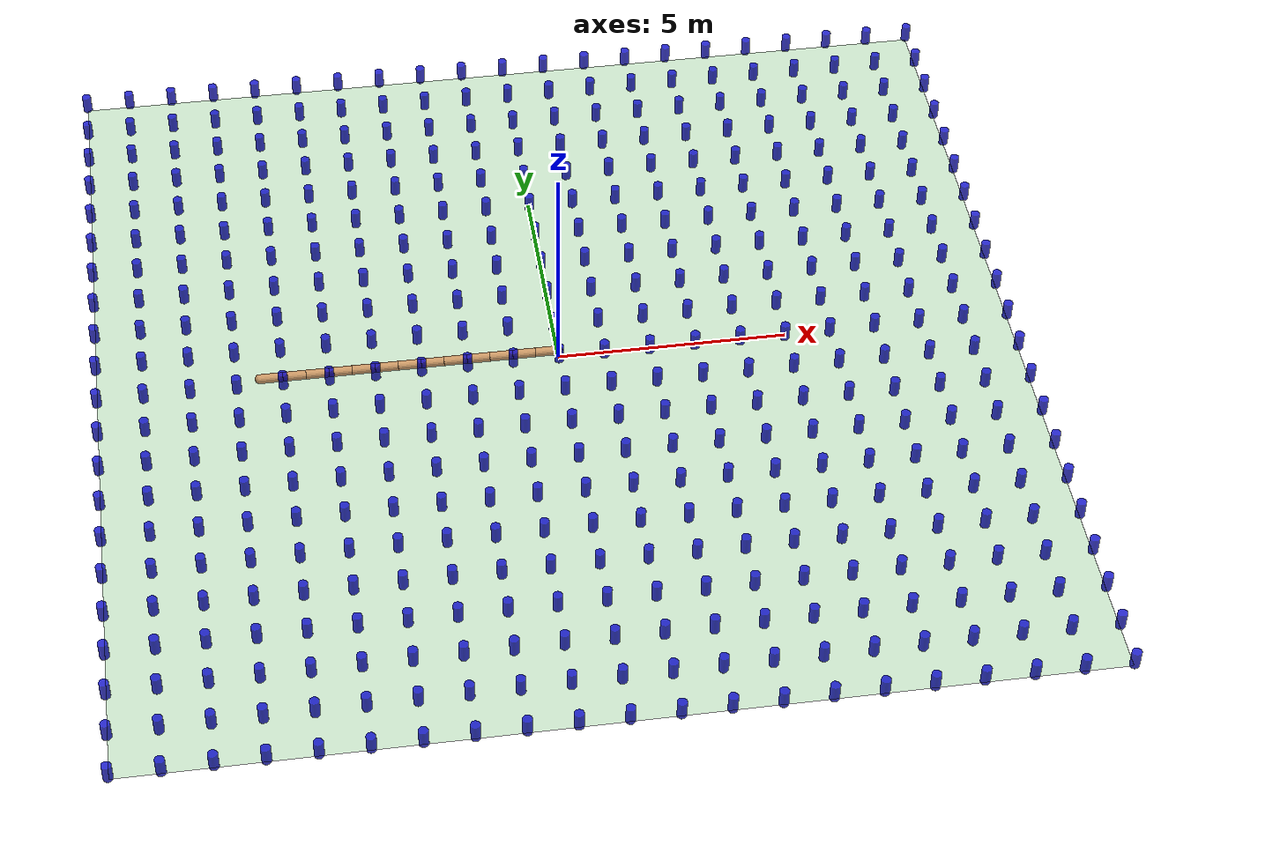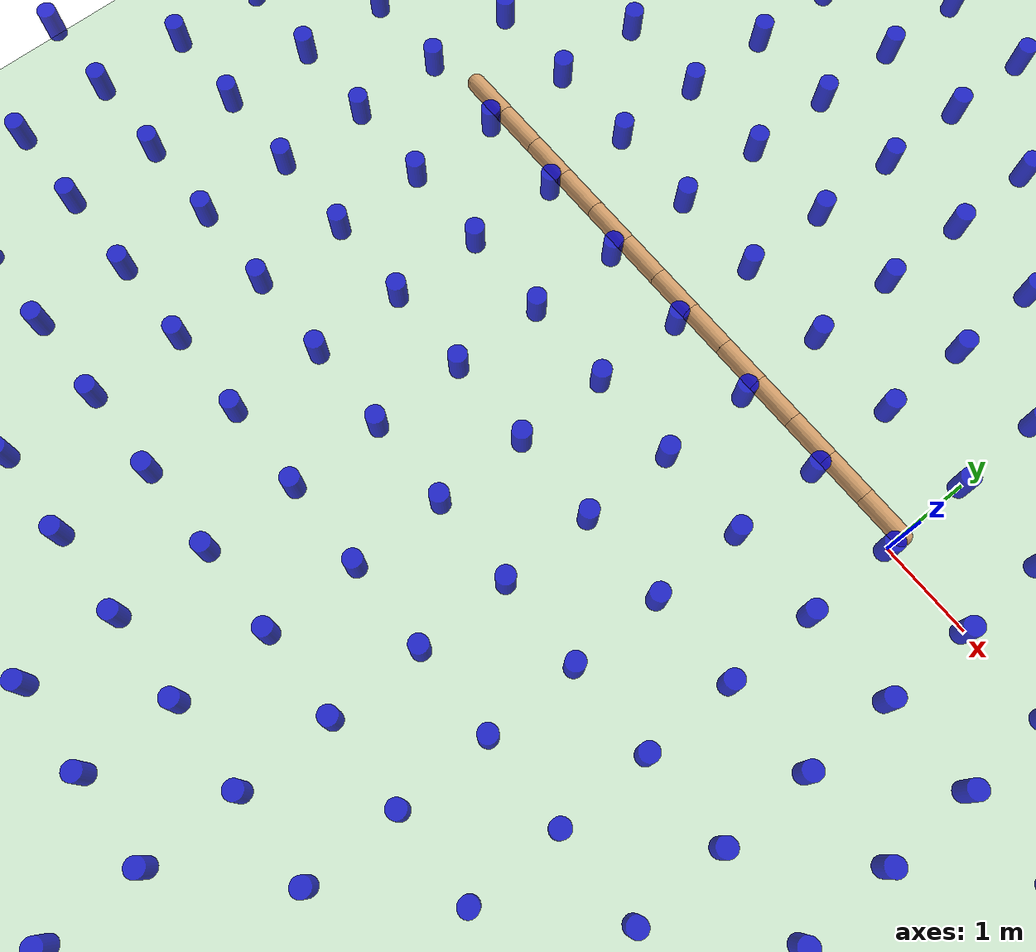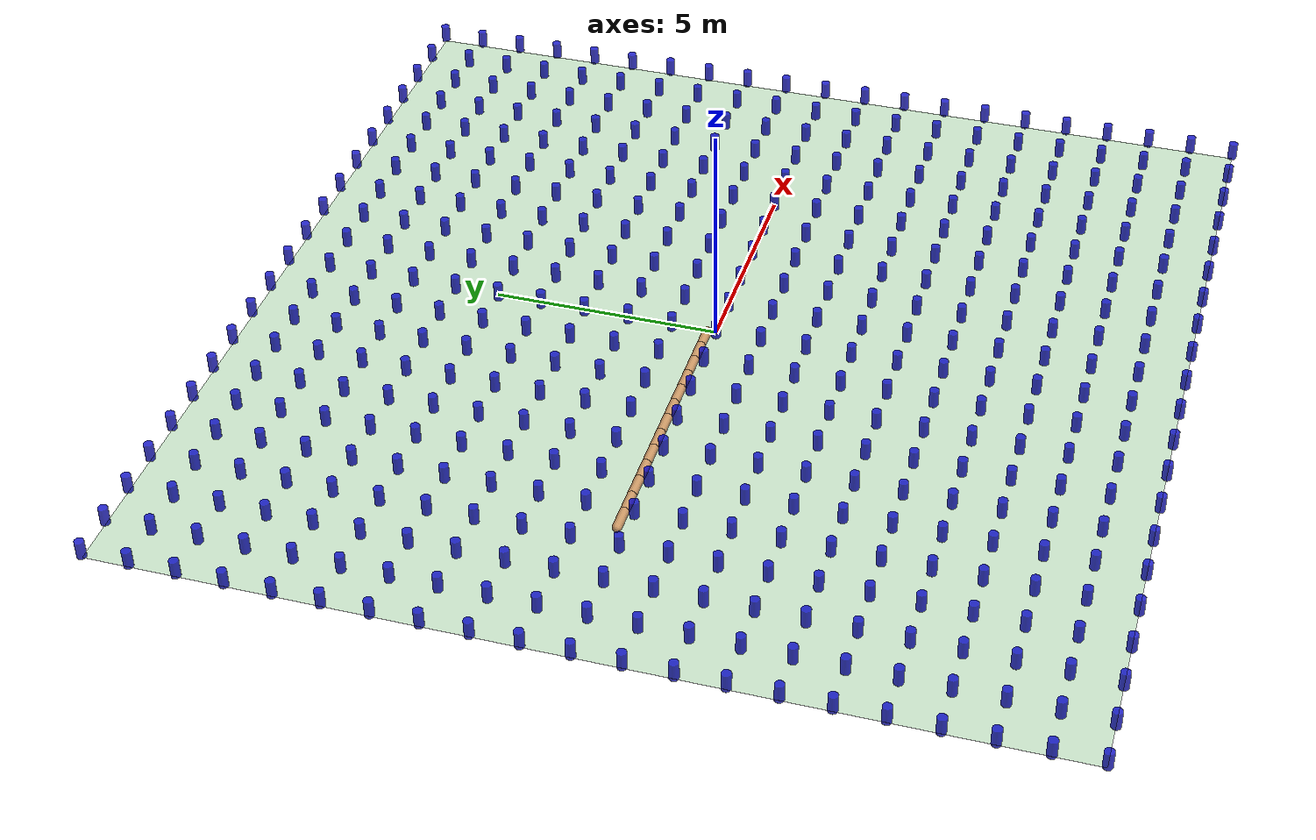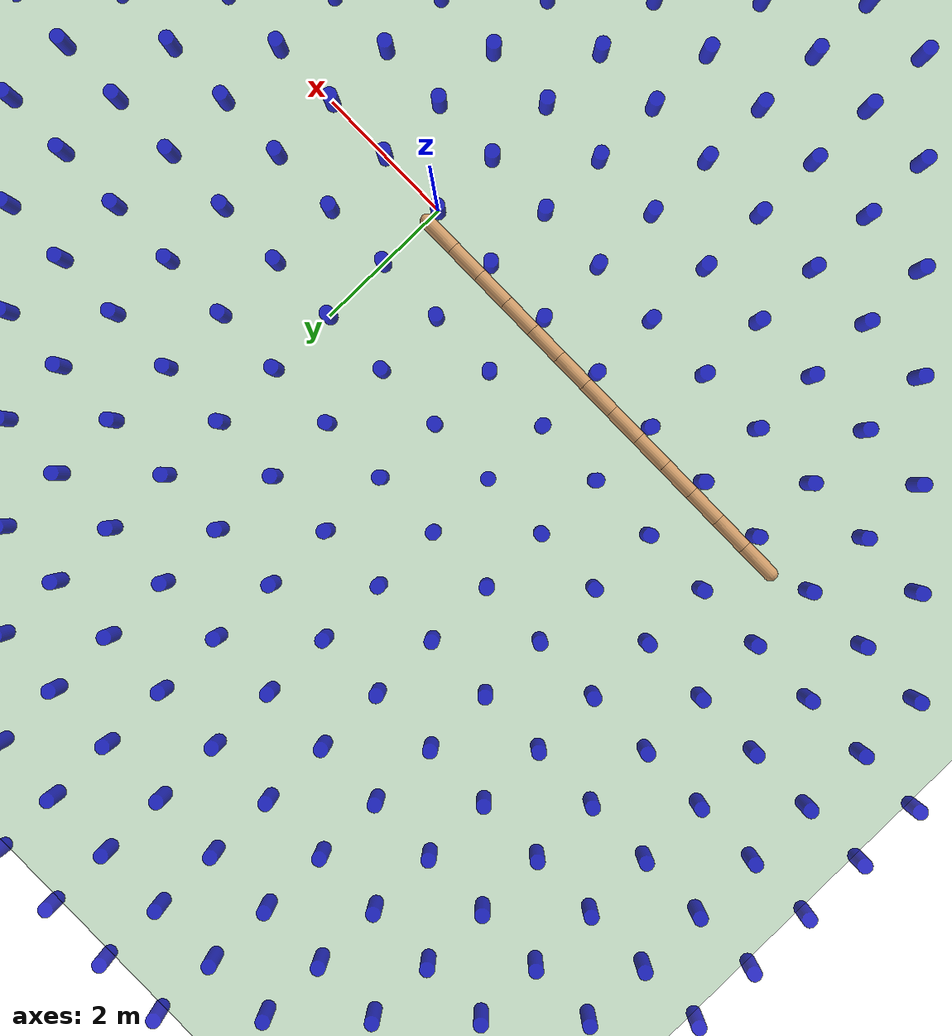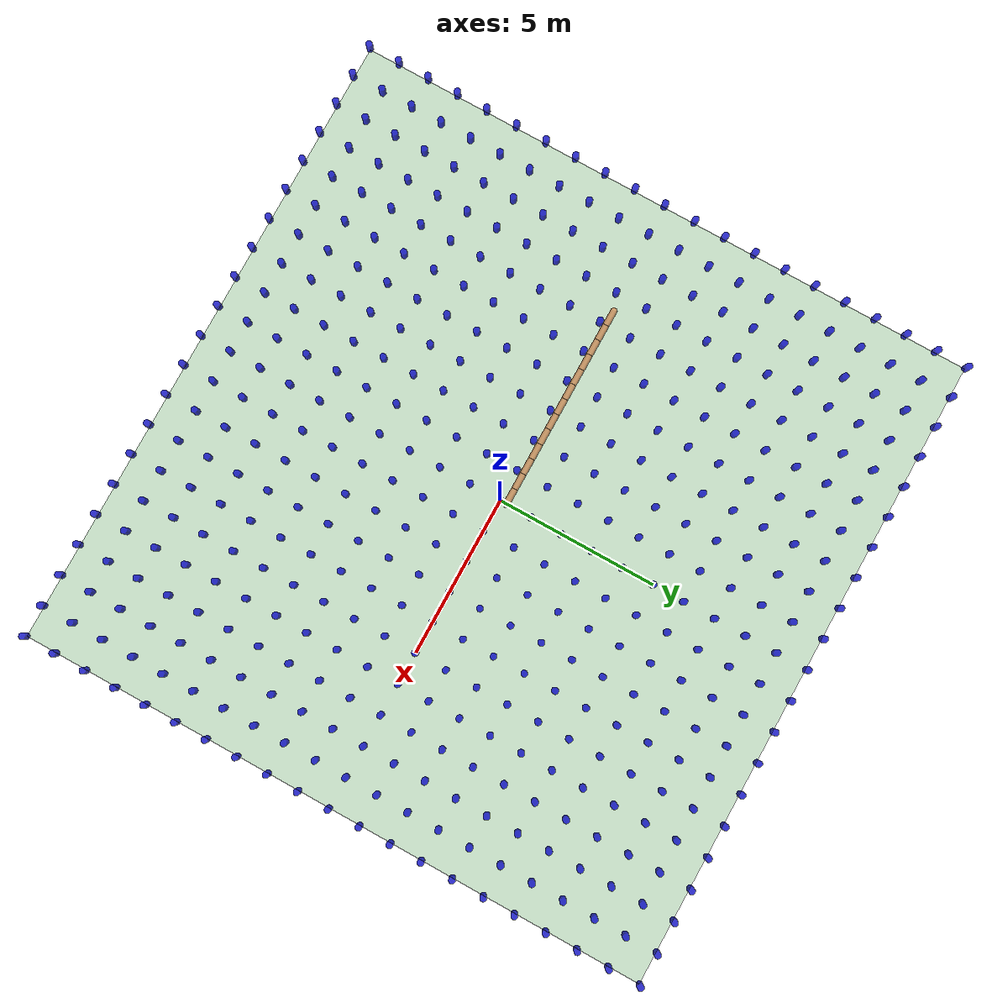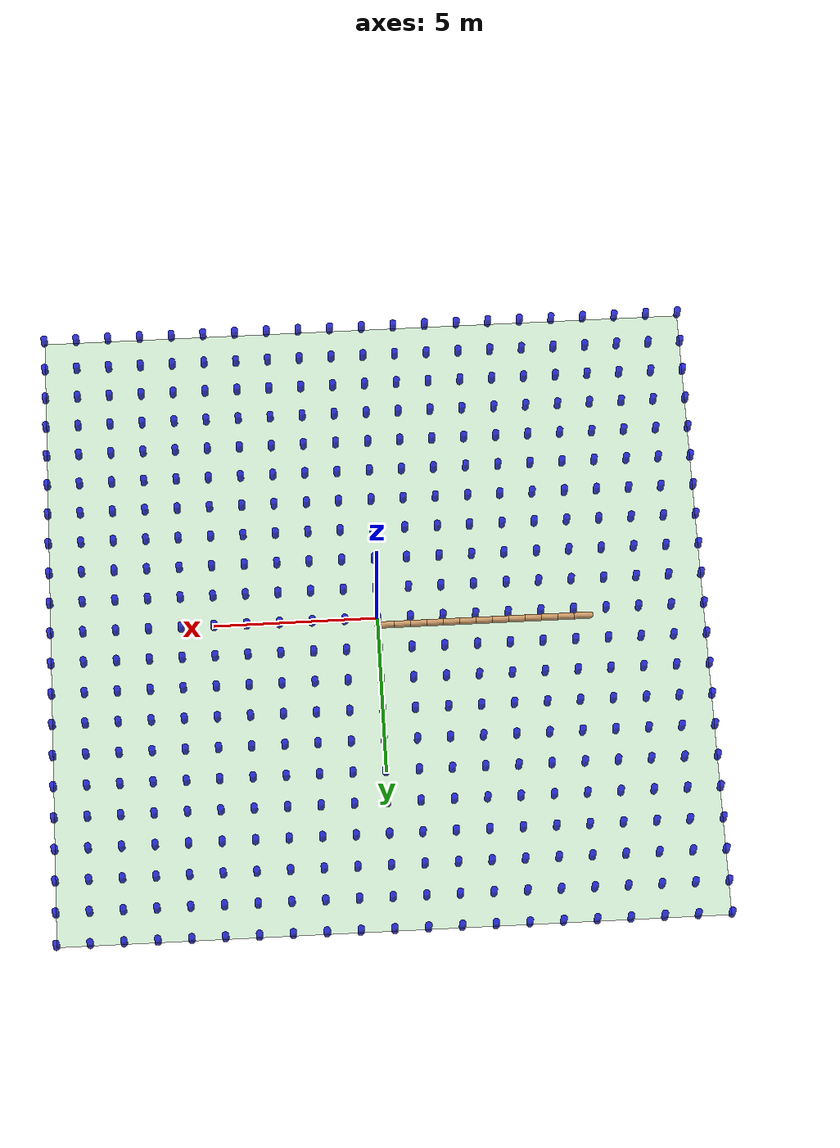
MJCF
<mujoco><compiler angle="degree" coordinate="local" inertiafromgeom="true" /><option collision="all" density="4000.0" integrator="RK4" timestep="0.01" viscosity="0.1" gravity="0 -9.80665 0" /><default><geom conaffinity="1" condim="1" contype="1" material="geom" rgba="0.8 0.6 .4 1" /><joint armature="0.1" /></default><asset><texture builtin="gradient" height="100" rgb1="1 1 1" rgb2="0 0 0" type="skybox" width="100" /><texture builtin="flat" height="1278" mark="cross" markrgb="1 1 1" name="texgeom" random="0.01" rgb1="0.8 0.6 0.4" rgb2="0.8 0.6 0.4" type="cube" width="127" /><texture builtin="checker" height="100" name="texplane" rgb1="0 0 0" rgb2="0.8 0.8 0.8" type="2d" width="100" /><material name="MatPlane" reflectance="0.5" shininess="1" specular="1" texrepeat="10 10" texture="texplane" /><material name="geom" texture="texgeom" texuniform="true" /></asset><worldbody><light cutoff="100" diffuse="1 1 1" dir="-0 0 -1.3" directional="true" exponent="1" pos="0 0 1.3" specular=".1 .1 .1" /><body name="floor" pos="0 0 0"><geom conaffinity="1" condim="3" material="MatPlane" name="floor_geom" pos="0 0 -0.1" rgba="0.8 0.9 0.8 1" size="10 10 0.1" type="plane" /><geom conaffinity="1" condim="3" name="cyl -10 -10" pos="-10 -10 0.1" rgba="0.0 0.0 0.8 0.8" size="0.1 0.2" type="cylinder" /><geom conaffinity="1" condim="3" name="cyl -10 -9" pos="-10 -9 0.1" rgba="0.0 0.0 0.8 0.8" size="0.1 0.2" type="cylinder" /><geom conaffinity="1" condim="3" name="cyl -10 -8" pos="-10 -8 0.1" rgba="0.0 0.0 0.8 0.8" size="0.1 0.2" type="cylinder" /><geom conaffinity="1" condim="3" name="cyl -10 -7" pos="-10 -7 0.1" rgba="0.0 0.0 0.8 0.8" size="0.1 0.2" type="cylinder" /><geom conaffinity="1" condim="3" name="cyl -10 -6" pos="-10 -6 0.1" rgba="0.0 0.0 0.8 0.8" size="0.1 0.2" type="cylinder" /><geom conaffinity="1" condim="3" name="cyl -10 -5" pos="-10 -5 0.1" rgba="0.0 0.0 0.8 0.8" size="0.1 0.2" type="cylinder" /><geom conaffinity="1" condim="3" name="cyl -10 -4" pos="-10 -4 0.1" rgba="0.0 0.0 0.8 0.8" size="0.1 0.2" type="cylinder" /><geom conaffinity="1" condim="3" name="cyl -10 -3" pos="-10 -3 0.1" rgba="0.0 0.0 0.8 0.8" size="0.1 0.2" type="cylinder" /><geom conaffinity="1" condim="3" name="cyl -10 -2" pos="-10 -2 0.1" rgba="0.0 0.0 0.8 0.8" size="0.1 0.2" type="cylinder" /><geom conaffinity="1" condim="3" name="cyl -10 -1" pos="-10 -1 0.1" rgba="0.0 0.0 0.8 0.8" size="0.1 0.2" type="cylinder" /><geom conaffinity="1" condim="3" name="cyl -10 0" pos="-10 0 0.1" rgba="0.0 0.0 0.8 0.8" size="0.1 0.2" type="cylinder" /><geom conaffinity="1" condim="3" name="cyl -10 1" pos="-10 1 0.1" rgba="0.0 0.0 0.8 0.8" size="0.1 0.2" type="cylinder" /><geom conaffinity="1" condim="3" name="cyl -10 2" pos="-10 2 0.1" rgba="0.0 0.0 0.8 0.8" size="0.1 0.2" type="cylinder" /><geom conaffinity="1" condim="3" name="cyl -10 3" pos="-10 3 0.1" rgba="0.0 0.0 0.8 0.8" size="0.1 0.2" type="cylinder" /><geom conaffinity="1" condim="3" name="cyl -10 4" pos="-10 4 0.1" rgba="0.0 0.0 0.8 0.8" size="0.1 0.2" type="cylinder" /><geom conaffinity="1" condim="3" name="cyl -10 5" pos="-10 5 0.1" rgba="0.0 0.0 0.8 0.8" size="0.1 0.2" type="cylinder" /><geom conaffinity="1" condim="3" name="cyl -10 6" pos="-10 6 0.1" rgba="0.0 0.0 0.8 0.8" size="0.1 0.2" type="cylinder" /><geom conaffinity="1" condim="3" name="cyl -10 7" pos="-10 7 0.1" rgba="0.0 0.0 0.8 0.8" size="0.1 0.2" type="cylinder" /><geom conaffinity="1" condim="3" name="cyl -10 8" pos="-10 8 0.1" rgba="0.0 0.0 0.8 0.8" size="0.1 0.2" type="cylinder" /><geom conaffinity="1" condim="3" name="cyl -10 9" pos="-10 9 0.1" rgba="0.0 0.0 0.8 0.8" size="0.1 0.2" type="cylinder" /><geom conaffinity="1" condim="3" name="cyl -10 10" pos="-10 10 0.1" rgba="0.0 0.0 0.8 0.8" size="0.1 0.2" type="cylinder" /><geom conaffinity="1" condim="3" name="cyl -9 -10" pos="-9 -10 0.1" rgba="0.0 0.0 0.8 0.8" size="0.1 0.2" type="cylinder" /><geom conaffinity="1" condim="3" name="cyl -9 -9" pos="-9 -9 0.1" rgba="0.0 0.0 0.8 0.8" size="0.1 0.2" type="cylinder" /><geom conaffinity="1" condim="3" name="cyl -9 -8" pos="-9 -8 0.1" rgba="0.0 0.0 0.8 0.8" size="0.1 0.2" type="cylinder" /><geom conaffinity="1" condim="3" name="cyl -9 -7" pos="-9 -7 0.1" rgba="0.0 0.0 0.8 0.8" size="0.1 0.2" type="cylinder" /><geom conaffinity="1" condim="3" name="cyl -9 -6" pos="-9 -6 0.1" rgba="0.0 0.0 0.8 0.8" size="0.1 0.2" type="cylinder" /><geom conaffinity="1" condim="3" name="cyl -9 -5" pos="-9 -5 0.1" rgba="0.0 0.0 0.8 0.8" size="0.1 0.2" type="cylinder" /><geom conaffinity="1" condim="3" name="cyl -9 -4" pos="-9 -4 0.1" rgba="0.0 0.0 0.8 0.8" size="0.1 0.2" type="cylinder" /><geom conaffinity="1" condim="3" name="cyl -9 -3" pos="-9 -3 0.1" rgba="0.0 0.0 0.8 0.8" size="0.1 0.2" type="cylinder" /><geom conaffinity="1" condim="3" name="cyl -9 -2" pos="-9 -2 0.1" rgba="0.0 0.0 0.8 0.8" size="0.1 0.2" type="cylinder" /><geom conaffinity="1" condim="3" name="cyl -9 -1" pos="-9 -1 0.1" rgba="0.0 0.0 0.8 0.8" size="0.1 0.2" type="cylinder" /><geom conaffinity="1" condim="3" name="cyl -9 0" pos="-9 0 0.1" rgba="0.0 0.0 0.8 0.8" size="0.1 0.2" type="cylinder" /><geom conaffinity="1" condim="3" name="cyl -9 1" pos="-9 1 0.1" rgba="0.0 0.0 0.8 0.8" size="0.1 0.2" type="cylinder" /><geom conaffinity="1" condim="3" name="cyl -9 2" pos="-9 2 0.1" rgba="0.0 0.0 0.8 0.8" size="0.1 0.2" type="cylinder" /><geom conaffinity="1" condim="3" name="cyl -9 3" pos="-9 3 0.1" rgba="0.0 0.0 0.8 0.8" size="0.1 0.2" type="cylinder" /><geom conaffinity="1" condim="3" name="cyl -9 4" pos="-9 4 0.1" rgba="0.0 0.0 0.8 0.8" size="0.1 0.2" type="cylinder" /><geom conaffinity="1" condim="3" name="cyl -9 5" pos="-9 5 0.1" rgba="0.0 0.0 0.8 0.8" size="0.1 0.2" type="cylinder" /><geom conaffinity="1" condim="3" name="cyl -9 6" pos="-9 6 0.1" rgba="0.0 0.0 0.8 0.8" size="0.1 0.2" type="cylinder" /><geom conaffinity="1" condim="3" name="cyl -9 7" pos="-9 7 0.1" rgba="0.0 0.0 0.8 0.8" size="0.1 0.2" type="cylinder" /><geom conaffinity="1" condim="3" name="cyl -9 8" pos="-9 8 0.1" rgba="0.0 0.0 0.8 0.8" size="0.1 0.2" type="cylinder" /><geom conaffinity="1" condim="3" name="cyl -9 9" pos="-9 9 0.1" rgba="0.0 0.0 0.8 0.8" size="0.1 0.2" type="cylinder" /><geom conaffinity="1" condim="3" name="cyl -9 10" pos="-9 10 0.1" rgba="0.0 0.0 0.8 0.8" size="0.1 0.2" type="cylinder" /><geom conaffinity="1" condim="3" name="cyl -8 -10" pos="-8 -10 0.1" rgba="0.0 0.0 0.8 0.8" size="0.1 0.2" type="cylinder" /><geom conaffinity="1" condim="3" name="cyl -8 -9" pos="-8 -9 0.1" rgba="0.0 0.0 0.8 0.8" size="0.1 0.2" type="cylinder" /><geom conaffinity="1" condim="3" name="cyl -8 -8" pos="-8 -8 0.1" rgba="0.0 0.0 0.8 0.8" size="0.1 0.2" type="cylinder" /><geom conaffinity="1" condim="3" name="cyl -8 -7" pos="-8 -7 0.1" rgba="0.0 0.0 0.8 0.8" size="0.1 0.2" type="cylinder" /><geom conaffinity="1" condim="3" name="cyl -8 -6" pos="-8 -6 0.1" rgba="0.0 0.0 0.8 0.8" size="0.1 0.2" type="cylinder" /><geom conaffinity="1" condim="3" name="cyl -8 -5" pos="-8 -5 0.1" rgba="0.0 0.0 0.8 0.8" size="0.1 0.2" type="cylinder" /><geom conaffinity="1" condim="3" name="cyl -8 -4" pos="-8 -4 0.1" rgba="0.0 0.0 0.8 0.8" size="0.1 0.2" type="cylinder" /><geom conaffinity="1" condim="3" name="cyl -8 -3" pos="-8 -3 0.1" rgba="0.0 0.0 0.8 0.8" size="0.1 0.2" type="cylinder" /><geom conaffinity="1" condim="3" name="cyl -8 -2" pos="-8 -2 0.1" rgba="0.0 0.0 0.8 0.8" size="0.1 0.2" type="cylinder" /><geom conaffinity="1" condim="3" name="cyl -8 -1" pos="-8 -1 0.1" rgba="0.0 0.0 0.8 0.8" size="0.1 0.2" type="cylinder" /><geom conaffinity="1" condim="3" name="cyl -8 0" pos="-8 0 0.1" rgba="0.0 0.0 0.8 0.8" size="0.1 0.2" type="cylinder" /><geom conaffinity="1" condim="3" name="cyl -8 1" pos="-8 1 0.1" rgba="0.0 0.0 0.8 0.8" size="0.1 0.2" type="cylinder" /><geom conaffinity="1" condim="3" name="cyl -8 2" pos="-8 2 0.1" rgba="0.0 0.0 0.8 0.8" size="0.1 0.2" type="cylinder" /><geom conaffinity="1" condim="3" name="cyl -8 3" pos="-8 3 0.1" rgba="0.0 0.0 0.8 0.8" size="0.1 0.2" type="cylinder" /><geom conaffinity="1" condim="3" name="cyl -8 4" pos="-8 4 0.1" rgba="0.0 0.0 0.8 0.8" size="0.1 0.2" type="cylinder" /><geom conaffinity="1" condim="3" name="cyl -8 5" pos="-8 5 0.1" rgba="0.0 0.0 0.8 0.8" size="0.1 0.2" type="cylinder" /><geom conaffinity="1" condim="3" name="cyl -8 6" pos="-8 6 0.1" rgba="0.0 0.0 0.8 0.8" size="0.1 0.2" type="cylinder" /><geom conaffinity="1" condim="3" name="cyl -8 7" pos="-8 7 0.1" rgba="0.0 0.0 0.8 0.8" size="0.1 0.2" type="cylinder" /><geom conaffinity="1" condim="3" name="cyl -8 8" pos="-8 8 0.1" rgba="0.0 0.0 0.8 0.8" size="0.1 0.2" type="cylinder" /><geom conaffinity="1" condim="3" name="cyl -8 9" pos="-8 9 0.1" rgba="0.0 0.0 0.8 0.8" size="0.1 0.2" type="cylinder" /><geom conaffinity="1" condim="3" name="cyl -8 10" pos="-8 10 0.1" rgba="0.0 0.0 0.8 0.8" size="0.1 0.2" type="cylinder" /><geom conaffinity="1" condim="3" name="cyl -7 -10" pos="-7 -10 0.1" rgba="0.0 0.0 0.8 0.8" size="0.1 0.2" type="cylinder" /><geom conaffinity="1" condim="3" name="cyl -7 -9" pos="-7 -9 0.1" rgba="0.0 0.0 0.8 0.8" size="0.1 0.2" type="cylinder" /><geom conaffinity="1" condim="3" name="cyl -7 -8" pos="-7 -8 0.1" rgba="0.0 0.0 0.8 0.8" size="0.1 0.2" type="cylinder" /><geom conaffinity="1" condim="3" name="cyl -7 -7" pos="-7 -7 0.1" rgba="0.0 0.0 0.8 0.8" size="0.1 0.2" type="cylinder" /><geom conaffinity="1" condim="3" name="cyl -7 -6" pos="-7 -6 0.1" rgba="0.0 0.0 0.8 0.8" size="0.1 0.2" type="cylinder" /><geom conaffinity="1" condim="3" name="cyl -7 -5" pos="-7 -5 0.1" rgba="0.0 0.0 0.8 0.8" size="0.1 0.2" type="cylinder" /><geom conaffinity="1" condim="3" name="cyl -7 -4" pos="-7 -4 0.1" rgba="0.0 0.0 0.8 0.8" size="0.1 0.2" type="cylinder" /><geom conaffinity="1" condim="3" name="cyl -7 -3" pos="-7 -3 0.1" rgba="0.0 0.0 0.8 0.8" size="0.1 0.2" type="cylinder" /><geom conaffinity="1" condim="3" name="cyl -7 -2" pos="-7 -2 0.1" rgba="0.0 0.0 0.8 0.8" size="0.1 0.2" type="cylinder" /><geom conaffinity="1" condim="3" name="cyl -7 -1" pos="-7 -1 0.1" rgba="0.0 0.0 0.8 0.8" size="0.1 0.2" type="cylinder" /><geom conaffinity="1" condim="3" name="cyl -7 0" pos="-7 0 0.1" rgba="0.0 0.0 0.8 0.8" size="0.1 0.2" type="cylinder" /><geom conaffinity="1" condim="3" name="cyl -7 1" pos="-7 1 0.1" rgba="0.0 0.0 0.8 0.8" size="0.1 0.2" type="cylinder" /><geom conaffinity="1" condim="3" name="cyl -7 2" pos="-7 2 0.1" rgba="0.0 0.0 0.8 0.8" size="0.1 0.2" type="cylinder" /><geom conaffinity="1" condim="3" name="cyl -7 3" pos="-7 3 0.1" rgba="0.0 0.0 0.8 0.8" size="0.1 0.2" type="cylinder" /><geom conaffinity="1" condim="3" name="cyl -7 4" pos="-7 4 0.1" rgba="0.0 0.0 0.8 0.8" size="0.1 0.2" type="cylinder" /><geom conaffinity="1" condim="3" name="cyl -7 5" pos="-7 5 0.1" rgba="0.0 0.0 0.8 0.8" size="0.1 0.2" type="cylinder" /><geom conaffinity="1" condim="3" name="cyl -7 6" pos="-7 6 0.1" rgba="0.0 0.0 0.8 0.8" size="0.1 0.2" type="cylinder" /><geom conaffinity="1" condim="3" name="cyl -7 7" pos="-7 7 0.1" rgba="0.0 0.0 0.8 0.8" size="0.1 0.2" type="cylinder" /><geom conaffinity="1" condim="3" name="cyl -7 8" pos="-7 8 0.1" rgba="0.0 0.0 0.8 0.8" size="0.1 0.2" type="cylinder" /><geom conaffinity="1" condim="3" name="cyl -7 9" pos="-7 9 0.1" rgba="0.0 0.0 0.8 0.8" size="0.1 0.2" type="cylinder" /><geom conaffinity="1" condim="3" name="cyl -7 10" pos="-7 10 0.1" rgba="0.0 0.0 0.8 0.8" size="0.1 0.2" type="cylinder" /><geom conaffinity="1" condim="3" name="cyl -6 -10" pos="-6 -10 0.1" rgba="0.0 0.0 0.8 0.8" size="0.1 0.2" type="cylinder" /><geom conaffinity="1" condim="3" name="cyl -6 -9" pos="-6 -9 0.1" rgba="0.0 0.0 0.8 0.8" size="0.1 0.2" type="cylinder" /><geom conaffinity="1" condim="3" name="cyl -6 -8" pos="-6 -8 0.1" rgba="0.0 0.0 0.8 0.8" size="0.1 0.2" type="cylinder" /><geom conaffinity="1" condim="3" name="cyl -6 -7" pos="-6 -7 0.1" rgba="0.0 0.0 0.8 0.8" size="0.1 0.2" type="cylinder" /><geom conaffinity="1" condim="3" name="cyl -6 -6" pos="-6 -6 0.1" rgba="0.0 0.0 0.8 0.8" size="0.1 0.2" type="cylinder" /><geom conaffinity="1" condim="3" name="cyl -6 -5" pos="-6 -5 0.1" rgba="0.0 0.0 0.8 0.8" size="0.1 0.2" type="cylinder" /><geom conaffinity="1" condim="3" name="cyl -6 -4" pos="-6 -4 0.1" rgba="0.0 0.0 0.8 0.8" size="0.1 0.2" type="cylinder" /><geom conaffinity="1" condim="3" name="cyl -6 -3" pos="-6 -3 0.1" rgba="0.0 0.0 0.8 0.8" size="0.1 0.2" type="cylinder" /><geom conaffinity="1" condim="3" name="cyl -6 -2" pos="-6 -2 0.1" rgba="0.0 0.0 0.8 0.8" size="0.1 0.2" type="cylinder" /><geom conaffinity="1" condim="3" name="cyl -6 -1" pos="-6 -1 0.1" rgba="0.0 0.0 0.8 0.8" size="0.1 0.2" type="cylinder" /><geom conaffinity="1" condim="3" name="cyl -6 0" pos="-6 0 0.1" rgba="0.0 0.0 0.8 0.8" size="0.1 0.2" type="cylinder" /><geom conaffinity="1" condim="3" name="cyl -6 1" pos="-6 1 0.1" rgba="0.0 0.0 0.8 0.8" size="0.1 0.2" type="cylinder" /><geom conaffinity="1" condim="3" name="cyl -6 2" pos="-6 2 0.1" rgba="0.0 0.0 0.8 0.8" size="0.1 0.2" type="cylinder" /><geom conaffinity="1" condim="3" name="cyl -6 3" pos="-6 3 0.1" rgba="0.0 0.0 0.8 0.8" size="0.1 0.2" type="cylinder" /><geom conaffinity="1" condim="3" name="cyl -6 4" pos="-6 4 0.1" rgba="0.0 0.0 0.8 0.8" size="0.1 0.2" type="cylinder" /><geom conaffinity="1" condim="3" name="cyl -6 5" pos="-6 5 0.1" rgba="0.0 0.0 0.8 0.8" size="0.1 0.2" type="cylinder" /><geom conaffinity="1" condim="3" name="cyl -6 6" pos="-6 6 0.1" rgba="0.0 0.0 0.8 0.8" size="0.1 0.2" type="cylinder" /><geom conaffinity="1" condim="3" name="cyl -6 7" pos="-6 7 0.1" rgba="0.0 0.0 0.8 0.8" size="0.1 0.2" type="cylinder" /><geom conaffinity="1" condim="3" name="cyl -6 8" pos="-6 8 0.1" rgba="0.0 0.0 0.8 0.8" size="0.1 0.2" type="cylinder" /><geom conaffinity="1" condim="3" name="cyl -6 9" pos="-6 9 0.1" rgba="0.0 0.0 0.8 0.8" size="0.1 0.2" type="cylinder" /><geom conaffinity="1" condim="3" name="cyl -6 10" pos="-6 10 0.1" rgba="0.0 0.0 0.8 0.8" size="0.1 0.2" type="cylinder" /><geom conaffinity="1" condim="3" name="cyl -5 -10" pos="-5 -10 0.1" rgba="0.0 0.0 0.8 0.8" size="0.1 0.2" type="cylinder" /><geom conaffinity="1" condim="3" name="cyl -5 -9" pos="-5 -9 0.1" rgba="0.0 0.0 0.8 0.8" size="0.1 0.2" type="cylinder" /><geom conaffinity="1" condim="3" name="cyl -5 -8" pos="-5 -8 0.1" rgba="0.0 0.0 0.8 0.8" size="0.1 0.2" type="cylinder" /><geom conaffinity="1" condim="3" name="cyl -5 -7" pos="-5 -7 0.1" rgba="0.0 0.0 0.8 0.8" size="0.1 0.2" type="cylinder" /><geom conaffinity="1" condim="3" name="cyl -5 -6" pos="-5 -6 0.1" rgba="0.0 0.0 0.8 0.8" size="0.1 0.2" type="cylinder" /><geom conaffinity="1" condim="3" name="cyl -5 -5" pos="-5 -5 0.1" rgba="0.0 0.0 0.8 0.8" size="0.1 0.2" type="cylinder" /><geom conaffinity="1" condim="3" name="cyl -5 -4" pos="-5 -4 0.1" rgba="0.0 0.0 0.8 0.8" size="0.1 0.2" type="cylinder" /><geom conaffinity="1" condim="3" name="cyl -5 -3" pos="-5 -3 0.1" rgba="0.0 0.0 0.8 0.8" size="0.1 0.2" type="cylinder" /><geom conaffinity="1" condim="3" name="cyl -5 -2" pos="-5 -2 0.1" rgba="0.0 0.0 0.8 0.8" size="0.1 0.2" type="cylinder" /><geom conaffinity="1" condim="3" name="cyl -5 -1" pos="-5 -1 0.1" rgba="0.0 0.0 0.8 0.8" size="0.1 0.2" type="cylinder" /><geom conaffinity="1" condim="3" name="cyl -5 0" pos="-5 0 0.1" rgba="0.0 0.0 0.8 0.8" size="0.1 0.2" type="cylinder" /><geom conaffinity="1" condim="3" name="cyl -5 1" pos="-5 1 0.1" rgba="0.0 0.0 0.8 0.8" size="0.1 0.2" type="cylinder" /><geom conaffinity="1" condim="3" name="cyl -5 2" pos="-5 2 0.1" rgba="0.0 0.0 0.8 0.8" size="0.1 0.2" type="cylinder" /><geom conaffinity="1" condim="3" name="cyl -5 3" pos="-5 3 0.1" rgba="0.0 0.0 0.8 0.8" size="0.1 0.2" type="cylinder" /><geom conaffinity="1" condim="3" name="cyl -5 4" pos="-5 4 0.1" rgba="0.0 0.0 0.8 0.8" size="0.1 0.2" type="cylinder" /><geom conaffinity="1" condim="3" name="cyl -5 5" pos="-5 5 0.1" rgba="0.0 0.0 0.8 0.8" size="0.1 0.2" type="cylinder" /><geom conaffinity="1" condim="3" name="cyl -5 6" pos="-5 6 0.1" rgba="0.0 0.0 0.8 0.8" size="0.1 0.2" type="cylinder" /><geom conaffinity="1" condim="3" name="cyl -5 7" pos="-5 7 0.1" rgba="0.0 0.0 0.8 0.8" size="0.1 0.2" type="cylinder" /><geom conaffinity="1" condim="3" name="cyl -5 8" pos="-5 8 0.1" rgba="0.0 0.0 0.8 0.8" size="0.1 0.2" type="cylinder" /><geom conaffinity="1" condim="3" name="cyl -5 9" pos="-5 9 0.1" rgba="0.0 0.0 0.8 0.8" size="0.1 0.2" type="cylinder" /><geom conaffinity="1" condim="3" name="cyl -5 10" pos="-5 10 0.1" rgba="0.0 0.0 0.8 0.8" size="0.1 0.2" type="cylinder" /><geom conaffinity="1" condim="3" name="cyl -4 -10" pos="-4 -10 0.1" rgba="0.0 0.0 0.8 0.8" size="0.1 0.2" type="cylinder" /><geom conaffinity="1" condim="3" name="cyl -4 -9" pos="-4 -9 0.1" rgba="0.0 0.0 0.8 0.8" size="0.1 0.2" type="cylinder" /><geom conaffinity="1" condim="3" name="cyl -4 -8" pos="-4 -8 0.1" rgba="0.0 0.0 0.8 0.8" size="0.1 0.2" type="cylinder" /><geom conaffinity="1" condim="3" name="cyl -4 -7" pos="-4 -7 0.1" rgba="0.0 0.0 0.8 0.8" size="0.1 0.2" type="cylinder" /><geom conaffinity="1" condim="3" name="cyl -4 -6" pos="-4 -6 0.1" rgba="0.0 0.0 0.8 0.8" size="0.1 0.2" type="cylinder" /><geom conaffinity="1" condim="3" name="cyl -4 -5" pos="-4 -5 0.1" rgba="0.0 0.0 0.8 0.8" size="0.1 0.2" type="cylinder" /><geom conaffinity="1" condim="3" name="cyl -4 -4" pos="-4 -4 0.1" rgba="0.0 0.0 0.8 0.8" size="0.1 0.2" type="cylinder" /><geom conaffinity="1" condim="3" name="cyl -4 -3" pos="-4 -3 0.1" rgba="0.0 0.0 0.8 0.8" size="0.1 0.2" type="cylinder" /><geom conaffinity="1" condim="3" name="cyl -4 -2" pos="-4 -2 0.1" rgba="0.0 0.0 0.8 0.8" size="0.1 0.2" type="cylinder" /><geom conaffinity="1" condim="3" name="cyl -4 -1" pos="-4 -1 0.1" rgba="0.0 0.0 0.8 0.8" size="0.1 0.2" type="cylinder" /><geom conaffinity="1" condim="3" name="cyl -4 0" pos="-4 0 0.1" rgba="0.0 0.0 0.8 0.8" size="0.1 0.2" type="cylinder" /><geom conaffinity="1" condim="3" name="cyl -4 1" pos="-4 1 0.1" rgba="0.0 0.0 0.8 0.8" size="0.1 0.2" type="cylinder" /><geom conaffinity="1" condim="3" name="cyl -4 2" pos="-4 2 0.1" rgba="0.0 0.0 0.8 0.8" size="0.1 0.2" type="cylinder" /><geom conaffinity="1" condim="3" name="cyl -4 3" pos="-4 3 0.1" rgba="0.0 0.0 0.8 0.8" size="0.1 0.2" type="cylinder" /><geom conaffinity="1" condim="3" name="cyl -4 4" pos="-4 4 0.1" rgba="0.0 0.0 0.8 0.8" size="0.1 0.2" type="cylinder" /><geom conaffinity="1" condim="3" name="cyl -4 5" pos="-4 5 0.1" rgba="0.0 0.0 0.8 0.8" size="0.1 0.2" type="cylinder" /><geom conaffinity="1" condim="3" name="cyl -4 6" pos="-4 6 0.1" rgba="0.0 0.0 0.8 0.8" size="0.1 0.2" type="cylinder" /><geom conaffinity="1" condim="3" name="cyl -4 7" pos="-4 7 0.1" rgba="0.0 0.0 0.8 0.8" size="0.1 0.2" type="cylinder" /><geom conaffinity="1" condim="3" name="cyl -4 8" pos="-4 8 0.1" rgba="0.0 0.0 0.8 0.8" size="0.1 0.2" type="cylinder" /><geom conaffinity="1" condim="3" name="cyl -4 9" pos="-4 9 0.1" rgba="0.0 0.0 0.8 0.8" size="0.1 0.2" type="cylinder" /><geom conaffinity="1" condim="3" name="cyl -4 10" pos="-4 10 0.1" rgba="0.0 0.0 0.8 0.8" size="0.1 0.2" type="cylinder" /><geom conaffinity="1" condim="3" name="cyl -3 -10" pos="-3 -10 0.1" rgba="0.0 0.0 0.8 0.8" size="0.1 0.2" type="cylinder" /><geom conaffinity="1" condim="3" name="cyl -3 -9" pos="-3 -9 0.1" rgba="0.0 0.0 0.8 0.8" size="0.1 0.2" type="cylinder" /><geom conaffinity="1" condim="3" name="cyl -3 -8" pos="-3 -8 0.1" rgba="0.0 0.0 0.8 0.8" size="0.1 0.2" type="cylinder" /><geom conaffinity="1" condim="3" name="cyl -3 -7" pos="-3 -7 0.1" rgba="0.0 0.0 0.8 0.8" size="0.1 0.2" type="cylinder" /><geom conaffinity="1" condim="3" name="cyl -3 -6" pos="-3 -6 0.1" rgba="0.0 0.0 0.8 0.8" size="0.1 0.2" type="cylinder" /><geom conaffinity="1" condim="3" name="cyl -3 -5" pos="-3 -5 0.1" rgba="0.0 0.0 0.8 0.8" size="0.1 0.2" type="cylinder" /><geom conaffinity="1" condim="3" name="cyl -3 -4" pos="-3 -4 0.1" rgba="0.0 0.0 0.8 0.8" size="0.1 0.2" type="cylinder" /><geom conaffinity="1" condim="3" name="cyl -3 -3" pos="-3 -3 0.1" rgba="0.0 0.0 0.8 0.8" size="0.1 0.2" type="cylinder" /><geom conaffinity="1" condim="3" name="cyl -3 -2" pos="-3 -2 0.1" rgba="0.0 0.0 0.8 0.8" size="0.1 0.2" type="cylinder" /><geom conaffinity="1" condim="3" name="cyl -3 -1" pos="-3 -1 0.1" rgba="0.0 0.0 0.8 0.8" size="0.1 0.2" type="cylinder" /><geom conaffinity="1" condim="3" name="cyl -3 0" pos="-3 0 0.1" rgba="0.0 0.0 0.8 0.8" size="0.1 0.2" type="cylinder" /><geom conaffinity="1" condim="3" name="cyl -3 1" pos="-3 1 0.1" rgba="0.0 0.0 0.8 0.8" size="0.1 0.2" type="cylinder" /><geom conaffinity="1" condim="3" name="cyl -3 2" pos="-3 2 0.1" rgba="0.0 0.0 0.8 0.8" size="0.1 0.2" type="cylinder" /><geom conaffinity="1" condim="3" name="cyl -3 3" pos="-3 3 0.1" rgba="0.0 0.0 0.8 0.8" size="0.1 0.2" type="cylinder" /><geom conaffinity="1" condim="3" name="cyl -3 4" pos="-3 4 0.1" rgba="0.0 0.0 0.8 0.8" size="0.1 0.2" type="cylinder" /><geom conaffinity="1" condim="3" name="cyl -3 5" pos="-3 5 0.1" rgba="0.0 0.0 0.8 0.8" size="0.1 0.2" type="cylinder" /><geom conaffinity="1" condim="3" name="cyl -3 6" pos="-3 6 0.1" rgba="0.0 0.0 0.8 0.8" size="0.1 0.2" type="cylinder" /><geom conaffinity="1" condim="3" name="cyl -3 7" pos="-3 7 0.1" rgba="0.0 0.0 0.8 0.8" size="0.1 0.2" type="cylinder" /><geom conaffinity="1" condim="3" name="cyl -3 8" pos="-3 8 0.1" rgba="0.0 0.0 0.8 0.8" size="0.1 0.2" type="cylinder" /><geom conaffinity="1" condim="3" name="cyl -3 9" pos="-3 9 0.1" rgba="0.0 0.0 0.8 0.8" size="0.1 0.2" type="cylinder" /><geom conaffinity="1" condim="3" name="cyl -3 10" pos="-3 10 0.1" rgba="0.0 0.0 0.8 0.8" size="0.1 0.2" type="cylinder" /><geom conaffinity="1" condim="3" name="cyl -2 -10" pos="-2 -10 0.1" rgba="0.0 0.0 0.8 0.8" size="0.1 0.2" type="cylinder" /><geom conaffinity="1" condim="3" name="cyl -2 -9" pos="-2 -9 0.1" rgba="0.0 0.0 0.8 0.8" size="0.1 0.2" type="cylinder" /><geom conaffinity="1" condim="3" name="cyl -2 -8" pos="-2 -8 0.1" rgba="0.0 0.0 0.8 0.8" size="0.1 0.2" type="cylinder" /><geom conaffinity="1" condim="3" name="cyl -2 -7" pos="-2 -7 0.1" rgba="0.0 0.0 0.8 0.8" size="0.1 0.2" type="cylinder" /><geom conaffinity="1" condim="3" name="cyl -2 -6" pos="-2 -6 0.1" rgba="0.0 0.0 0.8 0.8" size="0.1 0.2" type="cylinder" /><geom conaffinity="1" condim="3" name="cyl -2 -5" pos="-2 -5 0.1" rgba="0.0 0.0 0.8 0.8" size="0.1 0.2" type="cylinder" /><geom conaffinity="1" condim="3" name="cyl -2 -4" pos="-2 -4 0.1" rgba="0.0 0.0 0.8 0.8" size="0.1 0.2" type="cylinder" /><geom conaffinity="1" condim="3" name="cyl -2 -3" pos="-2 -3 0.1" rgba="0.0 0.0 0.8 0.8" size="0.1 0.2" type="cylinder" /><geom conaffinity="1" condim="3" name="cyl -2 -2" pos="-2 -2 0.1" rgba="0.0 0.0 0.8 0.8" size="0.1 0.2" type="cylinder" /><geom conaffinity="1" condim="3" name="cyl -2 -1" pos="-2 -1 0.1" rgba="0.0 0.0 0.8 0.8" size="0.1 0.2" type="cylinder" /><geom conaffinity="1" condim="3" name="cyl -2 0" pos="-2 0 0.1" rgba="0.0 0.0 0.8 0.8" size="0.1 0.2" type="cylinder" /><geom conaffinity="1" condim="3" name="cyl -2 1" pos="-2 1 0.1" rgba="0.0 0.0 0.8 0.8" size="0.1 0.2" type="cylinder" /><geom conaffinity="1" condim="3" name="cyl -2 2" pos="-2 2 0.1" rgba="0.0 0.0 0.8 0.8" size="0.1 0.2" type="cylinder" /><geom conaffinity="1" condim="3" name="cyl -2 3" pos="-2 3 0.1" rgba="0.0 0.0 0.8 0.8" size="0.1 0.2" type="cylinder" /><geom conaffinity="1" condim="3" name="cyl -2 4" pos="-2 4 0.1" rgba="0.0 0.0 0.8 0.8" size="0.1 0.2" type="cylinder" /><geom conaffinity="1" condim="3" name="cyl -2 5" pos="-2 5 0.1" rgba="0.0 0.0 0.8 0.8" size="0.1 0.2" type="cylinder" /><geom conaffinity="1" condim="3" name="cyl -2 6" pos="-2 6 0.1" rgba="0.0 0.0 0.8 0.8" size="0.1 0.2" type="cylinder" /><geom conaffinity="1" condim="3" name="cyl -2 7" pos="-2 7 0.1" rgba="0.0 0.0 0.8 0.8" size="0.1 0.2" type="cylinder" /><geom conaffinity="1" condim="3" name="cyl -2 8" pos="-2 8 0.1" rgba="0.0 0.0 0.8 0.8" size="0.1 0.2" type="cylinder" /><geom conaffinity="1" condim="3" name="cyl -2 9" pos="-2 9 0.1" rgba="0.0 0.0 0.8 0.8" size="0.1 0.2" type="cylinder" /><geom conaffinity="1" condim="3" name="cyl -2 10" pos="-2 10 0.1" rgba="0.0 0.0 0.8 0.8" size="0.1 0.2" type="cylinder" /><geom conaffinity="1" condim="3" name="cyl -1 -10" pos="-1 -10 0.1" rgba="0.0 0.0 0.8 0.8" size="0.1 0.2" type="cylinder" /><geom conaffinity="1" condim="3" name="cyl -1 -9" pos="-1 -9 0.1" rgba="0.0 0.0 0.8 0.8" size="0.1 0.2" type="cylinder" /><geom conaffinity="1" condim="3" name="cyl -1 -8" pos="-1 -8 0.1" rgba="0.0 0.0 0.8 0.8" size="0.1 0.2" type="cylinder" /><geom conaffinity="1" condim="3" name="cyl -1 -7" pos="-1 -7 0.1" rgba="0.0 0.0 0.8 0.8" size="0.1 0.2" type="cylinder" /><geom conaffinity="1" condim="3" name="cyl -1 -6" pos="-1 -6 0.1" rgba="0.0 0.0 0.8 0.8" size="0.1 0.2" type="cylinder" /><geom conaffinity="1" condim="3" name="cyl -1 -5" pos="-1 -5 0.1" rgba="0.0 0.0 0.8 0.8" size="0.1 0.2" type="cylinder" /><geom conaffinity="1" condim="3" name="cyl -1 -4" pos="-1 -4 0.1" rgba="0.0 0.0 0.8 0.8" size="0.1 0.2" type="cylinder" /><geom conaffinity="1" condim="3" name="cyl -1 -3" pos="-1 -3 0.1" rgba="0.0 0.0 0.8 0.8" size="0.1 0.2" type="cylinder" /><geom conaffinity="1" condim="3" name="cyl -1 -2" pos="-1 -2 0.1" rgba="0.0 0.0 0.8 0.8" size="0.1 0.2" type="cylinder" /><geom conaffinity="1" condim="3" name="cyl -1 -1" pos="-1 -1 0.1" rgba="0.0 0.0 0.8 0.8" size="0.1 0.2" type="cylinder" /><geom conaffinity="1" condim="3" name="cyl -1 0" pos="-1 0 0.1" rgba="0.0 0.0 0.8 0.8" size="0.1 0.2" type="cylinder" /><geom conaffinity="1" condim="3" name="cyl -1 1" pos="-1 1 0.1" rgba="0.0 0.0 0.8 0.8" size="0.1 0.2" type="cylinder" /><geom conaffinity="1" condim="3" name="cyl -1 2" pos="-1 2 0.1" rgba="0.0 0.0 0.8 0.8" size="0.1 0.2" type="cylinder" /><geom conaffinity="1" condim="3" name="cyl -1 3" pos="-1 3 0.1" rgba="0.0 0.0 0.8 0.8" size="0.1 0.2" type="cylinder" /><geom conaffinity="1" condim="3" name="cyl -1 4" pos="-1 4 0.1" rgba="0.0 0.0 0.8 0.8" size="0.1 0.2" type="cylinder" /><geom conaffinity="1" condim="3" name="cyl -1 5" pos="-1 5 0.1" rgba="0.0 0.0 0.8 0.8" size="0.1 0.2" type="cylinder" /><geom conaffinity="1" condim="3" name="cyl -1 6" pos="-1 6 0.1" rgba="0.0 0.0 0.8 0.8" size="0.1 0.2" type="cylinder" /><geom conaffinity="1" condim="3" name="cyl -1 7" pos="-1 7 0.1" rgba="0.0 0.0 0.8 0.8" size="0.1 0.2" type="cylinder" /><geom conaffinity="1" condim="3" name="cyl -1 8" pos="-1 8 0.1" rgba="0.0 0.0 0.8 0.8" size="0.1 0.2" type="cylinder" /><geom conaffinity="1" condim="3" name="cyl -1 9" pos="-1 9 0.1" rgba="0.0 0.0 0.8 0.8" size="0.1 0.2" type="cylinder" /><geom conaffinity="1" condim="3" name="cyl -1 10" pos="-1 10 0.1" rgba="0.0 0.0 0.8 0.8" size="0.1 0.2" type="cylinder" /><geom conaffinity="1" condim="3" name="cyl 0 -10" pos="0 -10 0.1" rgba="0.0 0.0 0.8 0.8" size="0.1 0.2" type="cylinder" /><geom conaffinity="1" condim="3" name="cyl 0 -9" pos="0 -9 0.1" rgba="0.0 0.0 0.8 0.8" size="0.1 0.2" type="cylinder" /><geom conaffinity="1" condim="3" name="cyl 0 -8" pos="0 -8 0.1" rgba="0.0 0.0 0.8 0.8" size="0.1 0.2" type="cylinder" /><geom conaffinity="1" condim="3" name="cyl 0 -7" pos="0 -7 0.1" rgba="0.0 0.0 0.8 0.8" size="0.1 0.2" type="cylinder" /><geom conaffinity="1" condim="3" name="cyl 0 -6" pos="0 -6 0.1" rgba="0.0 0.0 0.8 0.8" size="0.1 0.2" type="cylinder" /><geom conaffinity="1" condim="3" name="cyl 0 -5" pos="0 -5 0.1" rgba="0.0 0.0 0.8 0.8" size="0.1 0.2" type="cylinder" /><geom conaffinity="1" condim="3" name="cyl 0 -4" pos="0 -4 0.1" rgba="0.0 0.0 0.8 0.8" size="0.1 0.2" type="cylinder" /><geom conaffinity="1" condim="3" name="cyl 0 -3" pos="0 -3 0.1" rgba="0.0 0.0 0.8 0.8" size="0.1 0.2" type="cylinder" /><geom conaffinity="1" condim="3" name="cyl 0 -2" pos="0 -2 0.1" rgba="0.0 0.0 0.8 0.8" size="0.1 0.2" type="cylinder" /><geom conaffinity="1" condim="3" name="cyl 0 -1" pos="0 -1 0.1" rgba="0.0 0.0 0.8 0.8" size="0.1 0.2" type="cylinder" /><geom conaffinity="1" condim="3" name="cyl 0 0" pos="0 0 0.1" rgba="0.0 0.0 0.8 0.8" size="0.1 0.2" type="cylinder" /><geom conaffinity="1" condim="3" name="cyl 0 1" pos="0 1 0.1" rgba="0.0 0.0 0.8 0.8" size="0.1 0.2" type="cylinder" /><geom conaffinity="1" condim="3" name="cyl 0 2" pos="0 2 0.1" rgba="0.0 0.0 0.8 0.8" size="0.1 0.2" type="cylinder" /><geom conaffinity="1" condim="3" name="cyl 0 3" pos="0 3 0.1" rgba="0.0 0.0 0.8 0.8" size="0.1 0.2" type="cylinder" /><geom conaffinity="1" condim="3" name="cyl 0 4" pos="0 4 0.1" rgba="0.0 0.0 0.8 0.8" size="0.1 0.2" type="cylinder" /><geom conaffinity="1" condim="3" name="cyl 0 5" pos="0 5 0.1" rgba="0.0 0.0 0.8 0.8" size="0.1 0.2" type="cylinder" /><geom conaffinity="1" condim="3" name="cyl 0 6" pos="0 6 0.1" rgba="0.0 0.0 0.8 0.8" size="0.1 0.2" type="cylinder" /><geom conaffinity="1" condim="3" name="cyl 0 7" pos="0 7 0.1" rgba="0.0 0.0 0.8 0.8" size="0.1 0.2" type="cylinder" /><geom conaffinity="1" condim="3" name="cyl 0 8" pos="0 8 0.1" rgba="0.0 0.0 0.8 0.8" size="0.1 0.2" type="cylinder" /><geom conaffinity="1" condim="3" name="cyl 0 9" pos="0 9 0.1" rgba="0.0 0.0 0.8 0.8" size="0.1 0.2" type="cylinder" /><geom conaffinity="1" condim="3" name="cyl 0 10" pos="0 10 0.1" rgba="0.0 0.0 0.8 0.8" size="0.1 0.2" type="cylinder" /><geom conaffinity="1" condim="3" name="cyl 1 -10" pos="1 -10 0.1" rgba="0.0 0.0 0.8 0.8" size="0.1 0.2" type="cylinder" /><geom conaffinity="1" condim="3" name="cyl 1 -9" pos="1 -9 0.1" rgba="0.0 0.0 0.8 0.8" size="0.1 0.2" type="cylinder" /><geom conaffinity="1" condim="3" name="cyl 1 -8" pos="1 -8 0.1" rgba="0.0 0.0 0.8 0.8" size="0.1 0.2" type="cylinder" /><geom conaffinity="1" condim="3" name="cyl 1 -7" pos="1 -7 0.1" rgba="0.0 0.0 0.8 0.8" size="0.1 0.2" type="cylinder" /><geom conaffinity="1" condim="3" name="cyl 1 -6" pos="1 -6 0.1" rgba="0.0 0.0 0.8 0.8" size="0.1 0.2" type="cylinder" /><geom conaffinity="1" condim="3" name="cyl 1 -5" pos="1 -5 0.1" rgba="0.0 0.0 0.8 0.8" size="0.1 0.2" type="cylinder" /><geom conaffinity="1" condim="3" name="cyl 1 -4" pos="1 -4 0.1" rgba="0.0 0.0 0.8 0.8" size="0.1 0.2" type="cylinder" /><geom conaffinity="1" condim="3" name="cyl 1 -3" pos="1 -3 0.1" rgba="0.0 0.0 0.8 0.8" size="0.1 0.2" type="cylinder" /><geom conaffinity="1" condim="3" name="cyl 1 -2" pos="1 -2 0.1" rgba="0.0 0.0 0.8 0.8" size="0.1 0.2" type="cylinder" /><geom conaffinity="1" condim="3" name="cyl 1 -1" pos="1 -1 0.1" rgba="0.0 0.0 0.8 0.8" size="0.1 0.2" type="cylinder" /><geom conaffinity="1" condim="3" name="cyl 1 0" pos="1 0 0.1" rgba="0.0 0.0 0.8 0.8" size="0.1 0.2" type="cylinder" /><geom conaffinity="1" condim="3" name="cyl 1 1" pos="1 1 0.1" rgba="0.0 0.0 0.8 0.8" size="0.1 0.2" type="cylinder" /><geom conaffinity="1" condim="3" name="cyl 1 2" pos="1 2 0.1" rgba="0.0 0.0 0.8 0.8" size="0.1 0.2" type="cylinder" /><geom conaffinity="1" condim="3" name="cyl 1 3" pos="1 3 0.1" rgba="0.0 0.0 0.8 0.8" size="0.1 0.2" type="cylinder" /><geom conaffinity="1" condim="3" name="cyl 1 4" pos="1 4 0.1" rgba="0.0 0.0 0.8 0.8" size="0.1 0.2" type="cylinder" /><geom conaffinity="1" condim="3" name="cyl 1 5" pos="1 5 0.1" rgba="0.0 0.0 0.8 0.8" size="0.1 0.2" type="cylinder" /><geom conaffinity="1" condim="3" name="cyl 1 6" pos="1 6 0.1" rgba="0.0 0.0 0.8 0.8" size="0.1 0.2" type="cylinder" /><geom conaffinity="1" condim="3" name="cyl 1 7" pos="1 7 0.1" rgba="0.0 0.0 0.8 0.8" size="0.1 0.2" type="cylinder" /><geom conaffinity="1" condim="3" name="cyl 1 8" pos="1 8 0.1" rgba="0.0 0.0 0.8 0.8" size="0.1 0.2" type="cylinder" /><geom conaffinity="1" condim="3" name="cyl 1 9" pos="1 9 0.1" rgba="0.0 0.0 0.8 0.8" size="0.1 0.2" type="cylinder" /><geom conaffinity="1" condim="3" name="cyl 1 10" pos="1 10 0.1" rgba="0.0 0.0 0.8 0.8" size="0.1 0.2" type="cylinder" /><geom conaffinity="1" condim="3" name="cyl 2 -10" pos="2 -10 0.1" rgba="0.0 0.0 0.8 0.8" size="0.1 0.2" type="cylinder" /><geom conaffinity="1" condim="3" name="cyl 2 -9" pos="2 -9 0.1" rgba="0.0 0.0 0.8 0.8" size="0.1 0.2" type="cylinder" /><geom conaffinity="1" condim="3" name="cyl 2 -8" pos="2 -8 0.1" rgba="0.0 0.0 0.8 0.8" size="0.1 0.2" type="cylinder" /><geom conaffinity="1" condim="3" name="cyl 2 -7" pos="2 -7 0.1" rgba="0.0 0.0 0.8 0.8" size="0.1 0.2" type="cylinder" /><geom conaffinity="1" condim="3" name="cyl 2 -6" pos="2 -6 0.1" rgba="0.0 0.0 0.8 0.8" size="0.1 0.2" type="cylinder" /><geom conaffinity="1" condim="3" name="cyl 2 -5" pos="2 -5 0.1" rgba="0.0 0.0 0.8 0.8" size="0.1 0.2" type="cylinder" /><geom conaffinity="1" condim="3" name="cyl 2 -4" pos="2 -4 0.1" rgba="0.0 0.0 0.8 0.8" size="0.1 0.2" type="cylinder" /><geom conaffinity="1" condim="3" name="cyl 2 -3" pos="2 -3 0.1" rgba="0.0 0.0 0.8 0.8" size="0.1 0.2" type="cylinder" /><geom conaffinity="1" condim="3" name="cyl 2 -2" pos="2 -2 0.1" rgba="0.0 0.0 0.8 0.8" size="0.1 0.2" type="cylinder" /><geom conaffinity="1" condim="3" name="cyl 2 -1" pos="2 -1 0.1" rgba="0.0 0.0 0.8 0.8" size="0.1 0.2" type="cylinder" /><geom conaffinity="1" condim="3" name="cyl 2 0" pos="2 0 0.1" rgba="0.0 0.0 0.8 0.8" size="0.1 0.2" type="cylinder" /><geom conaffinity="1" condim="3" name="cyl 2 1" pos="2 1 0.1" rgba="0.0 0.0 0.8 0.8" size="0.1 0.2" type="cylinder" /><geom conaffinity="1" condim="3" name="cyl 2 2" pos="2 2 0.1" rgba="0.0 0.0 0.8 0.8" size="0.1 0.2" type="cylinder" /><geom conaffinity="1" condim="3" name="cyl 2 3" pos="2 3 0.1" rgba="0.0 0.0 0.8 0.8" size="0.1 0.2" type="cylinder" /><geom conaffinity="1" condim="3" name="cyl 2 4" pos="2 4 0.1" rgba="0.0 0.0 0.8 0.8" size="0.1 0.2" type="cylinder" /><geom conaffinity="1" condim="3" name="cyl 2 5" pos="2 5 0.1" rgba="0.0 0.0 0.8 0.8" size="0.1 0.2" type="cylinder" /><geom conaffinity="1" condim="3" name="cyl 2 6" pos="2 6 0.1" rgba="0.0 0.0 0.8 0.8" size="0.1 0.2" type="cylinder" /><geom conaffinity="1" condim="3" name="cyl 2 7" pos="2 7 0.1" rgba="0.0 0.0 0.8 0.8" size="0.1 0.2" type="cylinder" /><geom conaffinity="1" condim="3" name="cyl 2 8" pos="2 8 0.1" rgba="0.0 0.0 0.8 0.8" size="0.1 0.2" type="cylinder" /><geom conaffinity="1" condim="3" name="cyl 2 9" pos="2 9 0.1" rgba="0.0 0.0 0.8 0.8" size="0.1 0.2" type="cylinder" /><geom conaffinity="1" condim="3" name="cyl 2 10" pos="2 10 0.1" rgba="0.0 0.0 0.8 0.8" size="0.1 0.2" type="cylinder" /><geom conaffinity="1" condim="3" name="cyl 3 -10" pos="3 -10 0.1" rgba="0.0 0.0 0.8 0.8" size="0.1 0.2" type="cylinder" /><geom conaffinity="1" condim="3" name="cyl 3 -9" pos="3 -9 0.1" rgba="0.0 0.0 0.8 0.8" size="0.1 0.2" type="cylinder" /><geom conaffinity="1" condim="3" name="cyl 3 -8" pos="3 -8 0.1" rgba="0.0 0.0 0.8 0.8" size="0.1 0.2" type="cylinder" /><geom conaffinity="1" condim="3" name="cyl 3 -7" pos="3 -7 0.1" rgba="0.0 0.0 0.8 0.8" size="0.1 0.2" type="cylinder" /><geom conaffinity="1" condim="3" name="cyl 3 -6" pos="3 -6 0.1" rgba="0.0 0.0 0.8 0.8" size="0.1 0.2" type="cylinder" /><geom conaffinity="1" condim="3" name="cyl 3 -5" pos="3 -5 0.1" rgba="0.0 0.0 0.8 0.8" size="0.1 0.2" type="cylinder" /><geom conaffinity="1" condim="3" name="cyl 3 -4" pos="3 -4 0.1" rgba="0.0 0.0 0.8 0.8" size="0.1 0.2" type="cylinder" /><geom conaffinity="1" condim="3" name="cyl 3 -3" pos="3 -3 0.1" rgba="0.0 0.0 0.8 0.8" size="0.1 0.2" type="cylinder" /><geom conaffinity="1" condim="3" name="cyl 3 -2" pos="3 -2 0.1" rgba="0.0 0.0 0.8 0.8" size="0.1 0.2" type="cylinder" /><geom conaffinity="1" condim="3" name="cyl 3 -1" pos="3 -1 0.1" rgba="0.0 0.0 0.8 0.8" size="0.1 0.2" type="cylinder" /><geom conaffinity="1" condim="3" name="cyl 3 0" pos="3 0 0.1" rgba="0.0 0.0 0.8 0.8" size="0.1 0.2" type="cylinder" /><geom conaffinity="1" condim="3" name="cyl 3 1" pos="3 1 0.1" rgba="0.0 0.0 0.8 0.8" size="0.1 0.2" type="cylinder" /><geom conaffinity="1" condim="3" name="cyl 3 2" pos="3 2 0.1" rgba="0.0 0.0 0.8 0.8" size="0.1 0.2" type="cylinder" /><geom conaffinity="1" condim="3" name="cyl 3 3" pos="3 3 0.1" rgba="0.0 0.0 0.8 0.8" size="0.1 0.2" type="cylinder" /><geom conaffinity="1" condim="3" name="cyl 3 4" pos="3 4 0.1" rgba="0.0 0.0 0.8 0.8" size="0.1 0.2" type="cylinder" /><geom conaffinity="1" condim="3" name="cyl 3 5" pos="3 5 0.1" rgba="0.0 0.0 0.8 0.8" size="0.1 0.2" type="cylinder" /><geom conaffinity="1" condim="3" name="cyl 3 6" pos="3 6 0.1" rgba="0.0 0.0 0.8 0.8" size="0.1 0.2" type="cylinder" /><geom conaffinity="1" condim="3" name="cyl 3 7" pos="3 7 0.1" rgba="0.0 0.0 0.8 0.8" size="0.1 0.2" type="cylinder" /><geom conaffinity="1" condim="3" name="cyl 3 8" pos="3 8 0.1" rgba="0.0 0.0 0.8 0.8" size="0.1 0.2" type="cylinder" /><geom conaffinity="1" condim="3" name="cyl 3 9" pos="3 9 0.1" rgba="0.0 0.0 0.8 0.8" size="0.1 0.2" type="cylinder" /><geom conaffinity="1" condim="3" name="cyl 3 10" pos="3 10 0.1" rgba="0.0 0.0 0.8 0.8" size="0.1 0.2" type="cylinder" /><geom conaffinity="1" condim="3" name="cyl 4 -10" pos="4 -10 0.1" rgba="0.0 0.0 0.8 0.8" size="0.1 0.2" type="cylinder" /><geom conaffinity="1" condim="3" name="cyl 4 -9" pos="4 -9 0.1" rgba="0.0 0.0 0.8 0.8" size="0.1 0.2" type="cylinder" /><geom conaffinity="1" condim="3" name="cyl 4 -8" pos="4 -8 0.1" rgba="0.0 0.0 0.8 0.8" size="0.1 0.2" type="cylinder" /><geom conaffinity="1" condim="3" name="cyl 4 -7" pos="4 -7 0.1" rgba="0.0 0.0 0.8 0.8" size="0.1 0.2" type="cylinder" /><geom conaffinity="1" condim="3" name="cyl 4 -6" pos="4 -6 0.1" rgba="0.0 0.0 0.8 0.8" size="0.1 0.2" type="cylinder" /><geom conaffinity="1" condim="3" name="cyl 4 -5" pos="4 -5 0.1" rgba="0.0 0.0 0.8 0.8" size="0.1 0.2" type="cylinder" /><geom conaffinity="1" condim="3" name="cyl 4 -4" pos="4 -4 0.1" rgba="0.0 0.0 0.8 0.8" size="0.1 0.2" type="cylinder" /><geom conaffinity="1" condim="3" name="cyl 4 -3" pos="4 -3 0.1" rgba="0.0 0.0 0.8 0.8" size="0.1 0.2" type="cylinder" /><geom conaffinity="1" condim="3" name="cyl 4 -2" pos="4 -2 0.1" rgba="0.0 0.0 0.8 0.8" size="0.1 0.2" type="cylinder" /><geom conaffinity="1" condim="3" name="cyl 4 -1" pos="4 -1 0.1" rgba="0.0 0.0 0.8 0.8" size="0.1 0.2" type="cylinder" /><geom conaffinity="1" condim="3" name="cyl 4 0" pos="4 0 0.1" rgba="0.0 0.0 0.8 0.8" size="0.1 0.2" type="cylinder" /><geom conaffinity="1" condim="3" name="cyl 4 1" pos="4 1 0.1" rgba="0.0 0.0 0.8 0.8" size="0.1 0.2" type="cylinder" /><geom conaffinity="1" condim="3" name="cyl 4 2" pos="4 2 0.1" rgba="0.0 0.0 0.8 0.8" size="0.1 0.2" type="cylinder" /><geom conaffinity="1" condim="3" name="cyl 4 3" pos="4 3 0.1" rgba="0.0 0.0 0.8 0.8" size="0.1 0.2" type="cylinder" /><geom conaffinity="1" condim="3" name="cyl 4 4" pos="4 4 0.1" rgba="0.0 0.0 0.8 0.8" size="0.1 0.2" type="cylinder" /><geom conaffinity="1" condim="3" name="cyl 4 5" pos="4 5 0.1" rgba="0.0 0.0 0.8 0.8" size="0.1 0.2" type="cylinder" /><geom conaffinity="1" condim="3" name="cyl 4 6" pos="4 6 0.1" rgba="0.0 0.0 0.8 0.8" size="0.1 0.2" type="cylinder" /><geom conaffinity="1" condim="3" name="cyl 4 7" pos="4 7 0.1" rgba="0.0 0.0 0.8 0.8" size="0.1 0.2" type="cylinder" /><geom conaffinity="1" condim="3" name="cyl 4 8" pos="4 8 0.1" rgba="0.0 0.0 0.8 0.8" size="0.1 0.2" type="cylinder" /><geom conaffinity="1" condim="3" name="cyl 4 9" pos="4 9 0.1" rgba="0.0 0.0 0.8 0.8" size="0.1 0.2" type="cylinder" /><geom conaffinity="1" condim="3" name="cyl 4 10" pos="4 10 0.1" rgba="0.0 0.0 0.8 0.8" size="0.1 0.2" type="cylinder" /><geom conaffinity="1" condim="3" name="cyl 5 -10" pos="5 -10 0.1" rgba="0.0 0.0 0.8 0.8" size="0.1 0.2" type="cylinder" /><geom conaffinity="1" condim="3" name="cyl 5 -9" pos="5 -9 0.1" rgba="0.0 0.0 0.8 0.8" size="0.1 0.2" type="cylinder" /><geom conaffinity="1" condim="3" name="cyl 5 -8" pos="5 -8 0.1" rgba="0.0 0.0 0.8 0.8" size="0.1 0.2" type="cylinder" /><geom conaffinity="1" condim="3" name="cyl 5 -7" pos="5 -7 0.1" rgba="0.0 0.0 0.8 0.8" size="0.1 0.2" type="cylinder" /><geom conaffinity="1" condim="3" name="cyl 5 -6" pos="5 -6 0.1" rgba="0.0 0.0 0.8 0.8" size="0.1 0.2" type="cylinder" /><geom conaffinity="1" condim="3" name="cyl 5 -5" pos="5 -5 0.1" rgba="0.0 0.0 0.8 0.8" size="0.1 0.2" type="cylinder" /><geom conaffinity="1" condim="3" name="cyl 5 -4" pos="5 -4 0.1" rgba="0.0 0.0 0.8 0.8" size="0.1 0.2" type="cylinder" /><geom conaffinity="1" condim="3" name="cyl 5 -3" pos="5 -3 0.1" rgba="0.0 0.0 0.8 0.8" size="0.1 0.2" type="cylinder" /><geom conaffinity="1" condim="3" name="cyl 5 -2" pos="5 -2 0.1" rgba="0.0 0.0 0.8 0.8" size="0.1 0.2" type="cylinder" /><geom conaffinity="1" condim="3" name="cyl 5 -1" pos="5 -1 0.1" rgba="0.0 0.0 0.8 0.8" size="0.1 0.2" type="cylinder" /><geom conaffinity="1" condim="3" name="cyl 5 0" pos="5 0 0.1" rgba="0.0 0.0 0.8 0.8" size="0.1 0.2" type="cylinder" /><geom conaffinity="1" condim="3" name="cyl 5 1" pos="5 1 0.1" rgba="0.0 0.0 0.8 0.8" size="0.1 0.2" type="cylinder" /><geom conaffinity="1" condim="3" name="cyl 5 2" pos="5 2 0.1" rgba="0.0 0.0 0.8 0.8" size="0.1 0.2" type="cylinder" /><geom conaffinity="1" condim="3" name="cyl 5 3" pos="5 3 0.1" rgba="0.0 0.0 0.8 0.8" size="0.1 0.2" type="cylinder" /><geom conaffinity="1" condim="3" name="cyl 5 4" pos="5 4 0.1" rgba="0.0 0.0 0.8 0.8" size="0.1 0.2" type="cylinder" /><geom conaffinity="1" condim="3" name="cyl 5 5" pos="5 5 0.1" rgba="0.0 0.0 0.8 0.8" size="0.1 0.2" type="cylinder" /><geom conaffinity="1" condim="3" name="cyl 5 6" pos="5 6 0.1" rgba="0.0 0.0 0.8 0.8" size="0.1 0.2" type="cylinder" /><geom conaffinity="1" condim="3" name="cyl 5 7" pos="5 7 0.1" rgba="0.0 0.0 0.8 0.8" size="0.1 0.2" type="cylinder" /><geom conaffinity="1" condim="3" name="cyl 5 8" pos="5 8 0.1" rgba="0.0 0.0 0.8 0.8" size="0.1 0.2" type="cylinder" /><geom conaffinity="1" condim="3" name="cyl 5 9" pos="5 9 0.1" rgba="0.0 0.0 0.8 0.8" size="0.1 0.2" type="cylinder" /><geom conaffinity="1" condim="3" name="cyl 5 10" pos="5 10 0.1" rgba="0.0 0.0 0.8 0.8" size="0.1 0.2" type="cylinder" /><geom conaffinity="1" condim="3" name="cyl 6 -10" pos="6 -10 0.1" rgba="0.0 0.0 0.8 0.8" size="0.1 0.2" type="cylinder" /><geom conaffinity="1" condim="3" name="cyl 6 -9" pos="6 -9 0.1" rgba="0.0 0.0 0.8 0.8" size="0.1 0.2" type="cylinder" /><geom conaffinity="1" condim="3" name="cyl 6 -8" pos="6 -8 0.1" rgba="0.0 0.0 0.8 0.8" size="0.1 0.2" type="cylinder" /><geom conaffinity="1" condim="3" name="cyl 6 -7" pos="6 -7 0.1" rgba="0.0 0.0 0.8 0.8" size="0.1 0.2" type="cylinder" /><geom conaffinity="1" condim="3" name="cyl 6 -6" pos="6 -6 0.1" rgba="0.0 0.0 0.8 0.8" size="0.1 0.2" type="cylinder" /><geom conaffinity="1" condim="3" name="cyl 6 -5" pos="6 -5 0.1" rgba="0.0 0.0 0.8 0.8" size="0.1 0.2" type="cylinder" /><geom conaffinity="1" condim="3" name="cyl 6 -4" pos="6 -4 0.1" rgba="0.0 0.0 0.8 0.8" size="0.1 0.2" type="cylinder" /><geom conaffinity="1" condim="3" name="cyl 6 -3" pos="6 -3 0.1" rgba="0.0 0.0 0.8 0.8" size="0.1 0.2" type="cylinder" /><geom conaffinity="1" condim="3" name="cyl 6 -2" pos="6 -2 0.1" rgba="0.0 0.0 0.8 0.8" size="0.1 0.2" type="cylinder" /><geom conaffinity="1" condim="3" name="cyl 6 -1" pos="6 -1 0.1" rgba="0.0 0.0 0.8 0.8" size="0.1 0.2" type="cylinder" /><geom conaffinity="1" condim="3" name="cyl 6 0" pos="6 0 0.1" rgba="0.0 0.0 0.8 0.8" size="0.1 0.2" type="cylinder" /><geom conaffinity="1" condim="3" name="cyl 6 1" pos="6 1 0.1" rgba="0.0 0.0 0.8 0.8" size="0.1 0.2" type="cylinder" /><geom conaffinity="1" condim="3" name="cyl 6 2" pos="6 2 0.1" rgba="0.0 0.0 0.8 0.8" size="0.1 0.2" type="cylinder" /><geom conaffinity="1" condim="3" name="cyl 6 3" pos="6 3 0.1" rgba="0.0 0.0 0.8 0.8" size="0.1 0.2" type="cylinder" /><geom conaffinity="1" condim="3" name="cyl 6 4" pos="6 4 0.1" rgba="0.0 0.0 0.8 0.8" size="0.1 0.2" type="cylinder" /><geom conaffinity="1" condim="3" name="cyl 6 5" pos="6 5 0.1" rgba="0.0 0.0 0.8 0.8" size="0.1 0.2" type="cylinder" /><geom conaffinity="1" condim="3" name="cyl 6 6" pos="6 6 0.1" rgba="0.0 0.0 0.8 0.8" size="0.1 0.2" type="cylinder" /><geom conaffinity="1" condim="3" name="cyl 6 7" pos="6 7 0.1" rgba="0.0 0.0 0.8 0.8" size="0.1 0.2" type="cylinder" /><geom conaffinity="1" condim="3" name="cyl 6 8" pos="6 8 0.1" rgba="0.0 0.0 0.8 0.8" size="0.1 0.2" type="cylinder" /><geom conaffinity="1" condim="3" name="cyl 6 9" pos="6 9 0.1" rgba="0.0 0.0 0.8 0.8" size="0.1 0.2" type="cylinder" /><geom conaffinity="1" condim="3" name="cyl 6 10" pos="6 10 0.1" rgba="0.0 0.0 0.8 0.8" size="0.1 0.2" type="cylinder" /><geom conaffinity="1" condim="3" name="cyl 7 -10" pos="7 -10 0.1" rgba="0.0 0.0 0.8 0.8" size="0.1 0.2" type="cylinder" /><geom conaffinity="1" condim="3" name="cyl 7 -9" pos="7 -9 0.1" rgba="0.0 0.0 0.8 0.8" size="0.1 0.2" type="cylinder" /><geom conaffinity="1" condim="3" name="cyl 7 -8" pos="7 -8 0.1" rgba="0.0 0.0 0.8 0.8" size="0.1 0.2" type="cylinder" /><geom conaffinity="1" condim="3" name="cyl 7 -7" pos="7 -7 0.1" rgba="0.0 0.0 0.8 0.8" size="0.1 0.2" type="cylinder" /><geom conaffinity="1" condim="3" name="cyl 7 -6" pos="7 -6 0.1" rgba="0.0 0.0 0.8 0.8" size="0.1 0.2" type="cylinder" /><geom conaffinity="1" condim="3" name="cyl 7 -5" pos="7 -5 0.1" rgba="0.0 0.0 0.8 0.8" size="0.1 0.2" type="cylinder" /><geom conaffinity="1" condim="3" name="cyl 7 -4" pos="7 -4 0.1" rgba="0.0 0.0 0.8 0.8" size="0.1 0.2" type="cylinder" /><geom conaffinity="1" condim="3" name="cyl 7 -3" pos="7 -3 0.1" rgba="0.0 0.0 0.8 0.8" size="0.1 0.2" type="cylinder" /><geom conaffinity="1" condim="3" name="cyl 7 -2" pos="7 -2 0.1" rgba="0.0 0.0 0.8 0.8" size="0.1 0.2" type="cylinder" /><geom conaffinity="1" condim="3" name="cyl 7 -1" pos="7 -1 0.1" rgba="0.0 0.0 0.8 0.8" size="0.1 0.2" type="cylinder" /><geom conaffinity="1" condim="3" name="cyl 7 0" pos="7 0 0.1" rgba="0.0 0.0 0.8 0.8" size="0.1 0.2" type="cylinder" /><geom conaffinity="1" condim="3" name="cyl 7 1" pos="7 1 0.1" rgba="0.0 0.0 0.8 0.8" size="0.1 0.2" type="cylinder" /><geom conaffinity="1" condim="3" name="cyl 7 2" pos="7 2 0.1" rgba="0.0 0.0 0.8 0.8" size="0.1 0.2" type="cylinder" /><geom conaffinity="1" condim="3" name="cyl 7 3" pos="7 3 0.1" rgba="0.0 0.0 0.8 0.8" size="0.1 0.2" type="cylinder" /><geom conaffinity="1" condim="3" name="cyl 7 4" pos="7 4 0.1" rgba="0.0 0.0 0.8 0.8" size="0.1 0.2" type="cylinder" /><geom conaffinity="1" condim="3" name="cyl 7 5" pos="7 5 0.1" rgba="0.0 0.0 0.8 0.8" size="0.1 0.2" type="cylinder" /><geom conaffinity="1" condim="3" name="cyl 7 6" pos="7 6 0.1" rgba="0.0 0.0 0.8 0.8" size="0.1 0.2" type="cylinder" /><geom conaffinity="1" condim="3" name="cyl 7 7" pos="7 7 0.1" rgba="0.0 0.0 0.8 0.8" size="0.1 0.2" type="cylinder" /><geom conaffinity="1" condim="3" name="cyl 7 8" pos="7 8 0.1" rgba="0.0 0.0 0.8 0.8" size="0.1 0.2" type="cylinder" /><geom conaffinity="1" condim="3" name="cyl 7 9" pos="7 9 0.1" rgba="0.0 0.0 0.8 0.8" size="0.1 0.2" type="cylinder" /><geom conaffinity="1" condim="3" name="cyl 7 10" pos="7 10 0.1" rgba="0.0 0.0 0.8 0.8" size="0.1 0.2" type="cylinder" /><geom conaffinity="1" condim="3" name="cyl 8 -10" pos="8 -10 0.1" rgba="0.0 0.0 0.8 0.8" size="0.1 0.2" type="cylinder" /><geom conaffinity="1" condim="3" name="cyl 8 -9" pos="8 -9 0.1" rgba="0.0 0.0 0.8 0.8" size="0.1 0.2" type="cylinder" /><geom conaffinity="1" condim="3" name="cyl 8 -8" pos="8 -8 0.1" rgba="0.0 0.0 0.8 0.8" size="0.1 0.2" type="cylinder" /><geom conaffinity="1" condim="3" name="cyl 8 -7" pos="8 -7 0.1" rgba="0.0 0.0 0.8 0.8" size="0.1 0.2" type="cylinder" /><geom conaffinity="1" condim="3" name="cyl 8 -6" pos="8 -6 0.1" rgba="0.0 0.0 0.8 0.8" size="0.1 0.2" type="cylinder" /><geom conaffinity="1" condim="3" name="cyl 8 -5" pos="8 -5 0.1" rgba="0.0 0.0 0.8 0.8" size="0.1 0.2" type="cylinder" /><geom conaffinity="1" condim="3" name="cyl 8 -4" pos="8 -4 0.1" rgba="0.0 0.0 0.8 0.8" size="0.1 0.2" type="cylinder" /><geom conaffinity="1" condim="3" name="cyl 8 -3" pos="8 -3 0.1" rgba="0.0 0.0 0.8 0.8" size="0.1 0.2" type="cylinder" /><geom conaffinity="1" condim="3" name="cyl 8 -2" pos="8 -2 0.1" rgba="0.0 0.0 0.8 0.8" size="0.1 0.2" type="cylinder" /><geom conaffinity="1" condim="3" name="cyl 8 -1" pos="8 -1 0.1" rgba="0.0 0.0 0.8 0.8" size="0.1 0.2" type="cylinder" /><geom conaffinity="1" condim="3" name="cyl 8 0" pos="8 0 0.1" rgba="0.0 0.0 0.8 0.8" size="0.1 0.2" type="cylinder" /><geom conaffinity="1" condim="3" name="cyl 8 1" pos="8 1 0.1" rgba="0.0 0.0 0.8 0.8" size="0.1 0.2" type="cylinder" /><geom conaffinity="1" condim="3" name="cyl 8 2" pos="8 2 0.1" rgba="0.0 0.0 0.8 0.8" size="0.1 0.2" type="cylinder" /><geom conaffinity="1" condim="3" name="cyl 8 3" pos="8 3 0.1" rgba="0.0 0.0 0.8 0.8" size="0.1 0.2" type="cylinder" /><geom conaffinity="1" condim="3" name="cyl 8 4" pos="8 4 0.1" rgba="0.0 0.0 0.8 0.8" size="0.1 0.2" type="cylinder" /><geom conaffinity="1" condim="3" name="cyl 8 5" pos="8 5 0.1" rgba="0.0 0.0 0.8 0.8" size="0.1 0.2" type="cylinder" /><geom conaffinity="1" condim="3" name="cyl 8 6" pos="8 6 0.1" rgba="0.0 0.0 0.8 0.8" size="0.1 0.2" type="cylinder" /><geom conaffinity="1" condim="3" name="cyl 8 7" pos="8 7 0.1" rgba="0.0 0.0 0.8 0.8" size="0.1 0.2" type="cylinder" /><geom conaffinity="1" condim="3" name="cyl 8 8" pos="8 8 0.1" rgba="0.0 0.0 0.8 0.8" size="0.1 0.2" type="cylinder" /><geom conaffinity="1" condim="3" name="cyl 8 9" pos="8 9 0.1" rgba="0.0 0.0 0.8 0.8" size="0.1 0.2" type="cylinder" /><geom conaffinity="1" condim="3" name="cyl 8 10" pos="8 10 0.1" rgba="0.0 0.0 0.8 0.8" size="0.1 0.2" type="cylinder" /><geom conaffinity="1" condim="3" name="cyl 9 -10" pos="9 -10 0.1" rgba="0.0 0.0 0.8 0.8" size="0.1 0.2" type="cylinder" /><geom conaffinity="1" condim="3" name="cyl 9 -9" pos="9 -9 0.1" rgba="0.0 0.0 0.8 0.8" size="0.1 0.2" type="cylinder" /><geom conaffinity="1" condim="3" name="cyl 9 -8" pos="9 -8 0.1" rgba="0.0 0.0 0.8 0.8" size="0.1 0.2" type="cylinder" /><geom conaffinity="1" condim="3" name="cyl 9 -7" pos="9 -7 0.1" rgba="0.0 0.0 0.8 0.8" size="0.1 0.2" type="cylinder" /><geom conaffinity="1" condim="3" name="cyl 9 -6" pos="9 -6 0.1" rgba="0.0 0.0 0.8 0.8" size="0.1 0.2" type="cylinder" /><geom conaffinity="1" condim="3" name="cyl 9 -5" pos="9 -5 0.1" rgba="0.0 0.0 0.8 0.8" size="0.1 0.2" type="cylinder" /><geom conaffinity="1" condim="3" name="cyl 9 -4" pos="9 -4 0.1" rgba="0.0 0.0 0.8 0.8" size="0.1 0.2" type="cylinder" /><geom conaffinity="1" condim="3" name="cyl 9 -3" pos="9 -3 0.1" rgba="0.0 0.0 0.8 0.8" size="0.1 0.2" type="cylinder" /><geom conaffinity="1" condim="3" name="cyl 9 -2" pos="9 -2 0.1" rgba="0.0 0.0 0.8 0.8" size="0.1 0.2" type="cylinder" /><geom conaffinity="1" condim="3" name="cyl 9 -1" pos="9 -1 0.1" rgba="0.0 0.0 0.8 0.8" size="0.1 0.2" type="cylinder" /><geom conaffinity="1" condim="3" name="cyl 9 0" pos="9 0 0.1" rgba="0.0 0.0 0.8 0.8" size="0.1 0.2" type="cylinder" /><geom conaffinity="1" condim="3" name="cyl 9 1" pos="9 1 0.1" rgba="0.0 0.0 0.8 0.8" size="0.1 0.2" type="cylinder" /><geom conaffinity="1" condim="3" name="cyl 9 2" pos="9 2 0.1" rgba="0.0 0.0 0.8 0.8" size="0.1 0.2" type="cylinder" /><geom conaffinity="1" condim="3" name="cyl 9 3" pos="9 3 0.1" rgba="0.0 0.0 0.8 0.8" size="0.1 0.2" type="cylinder" /><geom conaffinity="1" condim="3" name="cyl 9 4" pos="9 4 0.1" rgba="0.0 0.0 0.8 0.8" size="0.1 0.2" type="cylinder" /><geom conaffinity="1" condim="3" name="cyl 9 5" pos="9 5 0.1" rgba="0.0 0.0 0.8 0.8" size="0.1 0.2" type="cylinder" /><geom conaffinity="1" condim="3" name="cyl 9 6" pos="9 6 0.1" rgba="0.0 0.0 0.8 0.8" size="0.1 0.2" type="cylinder" /><geom conaffinity="1" condim="3" name="cyl 9 7" pos="9 7 0.1" rgba="0.0 0.0 0.8 0.8" size="0.1 0.2" type="cylinder" /><geom conaffinity="1" condim="3" name="cyl 9 8" pos="9 8 0.1" rgba="0.0 0.0 0.8 0.8" size="0.1 0.2" type="cylinder" /><geom conaffinity="1" condim="3" name="cyl 9 9" pos="9 9 0.1" rgba="0.0 0.0 0.8 0.8" size="0.1 0.2" type="cylinder" /><geom conaffinity="1" condim="3" name="cyl 9 10" pos="9 10 0.1" rgba="0.0 0.0 0.8 0.8" size="0.1 0.2" type="cylinder" /><geom conaffinity="1" condim="3" name="cyl 10 -10" pos="10 -10 0.1" rgba="0.0 0.0 0.8 0.8" size="0.1 0.2" type="cylinder" /><geom conaffinity="1" condim="3" name="cyl 10 -9" pos="10 -9 0.1" rgba="0.0 0.0 0.8 0.8" size="0.1 0.2" type="cylinder" /><geom conaffinity="1" condim="3" name="cyl 10 -8" pos="10 -8 0.1" rgba="0.0 0.0 0.8 0.8" size="0.1 0.2" type="cylinder" /><geom conaffinity="1" condim="3" name="cyl 10 -7" pos="10 -7 0.1" rgba="0.0 0.0 0.8 0.8" size="0.1 0.2" type="cylinder" /><geom conaffinity="1" condim="3" name="cyl 10 -6" pos="10 -6 0.1" rgba="0.0 0.0 0.8 0.8" size="0.1 0.2" type="cylinder" /><geom conaffinity="1" condim="3" name="cyl 10 -5" pos="10 -5 0.1" rgba="0.0 0.0 0.8 0.8" size="0.1 0.2" type="cylinder" /><geom conaffinity="1" condim="3" name="cyl 10 -4" pos="10 -4 0.1" rgba="0.0 0.0 0.8 0.8" size="0.1 0.2" type="cylinder" /><geom conaffinity="1" condim="3" name="cyl 10 -3" pos="10 -3 0.1" rgba="0.0 0.0 0.8 0.8" size="0.1 0.2" type="cylinder" /><geom conaffinity="1" condim="3" name="cyl 10 -2" pos="10 -2 0.1" rgba="0.0 0.0 0.8 0.8" size="0.1 0.2" type="cylinder" /><geom conaffinity="1" condim="3" name="cyl 10 -1" pos="10 -1 0.1" rgba="0.0 0.0 0.8 0.8" size="0.1 0.2" type="cylinder" /><geom conaffinity="1" condim="3" name="cyl 10 0" pos="10 0 0.1" rgba="0.0 0.0 0.8 0.8" size="0.1 0.2" type="cylinder" /><geom conaffinity="1" condim="3" name="cyl 10 1" pos="10 1 0.1" rgba="0.0 0.0 0.8 0.8" size="0.1 0.2" type="cylinder" /><geom conaffinity="1" condim="3" name="cyl 10 2" pos="10 2 0.1" rgba="0.0 0.0 0.8 0.8" size="0.1 0.2" type="cylinder" /><geom conaffinity="1" condim="3" name="cyl 10 3" pos="10 3 0.1" rgba="0.0 0.0 0.8 0.8" size="0.1 0.2" type="cylinder" /><geom conaffinity="1" condim="3" name="cyl 10 4" pos="10 4 0.1" rgba="0.0 0.0 0.8 0.8" size="0.1 0.2" type="cylinder" /><geom conaffinity="1" condim="3" name="cyl 10 5" pos="10 5 0.1" rgba="0.0 0.0 0.8 0.8" size="0.1 0.2" type="cylinder" /><geom conaffinity="1" condim="3" name="cyl 10 6" pos="10 6 0.1" rgba="0.0 0.0 0.8 0.8" size="0.1 0.2" type="cylinder" /><geom conaffinity="1" condim="3" name="cyl 10 7" pos="10 7 0.1" rgba="0.0 0.0 0.8 0.8" size="0.1 0.2" type="cylinder" /><geom conaffinity="1" condim="3" name="cyl 10 8" pos="10 8 0.1" rgba="0.0 0.0 0.8 0.8" size="0.1 0.2" type="cylinder" /><geom conaffinity="1" condim="3" name="cyl 10 9" pos="10 9 0.1" rgba="0.0 0.0 0.8 0.8" size="0.1 0.2" type="cylinder" /><geom conaffinity="1" condim="3" name="cyl 10 10" pos="10 10 0.1" rgba="0.0 0.0 0.8 0.8" size="0.1 0.2" type="cylinder" /></body><body name="torso" pos="0 0.2 0"><camera name="track" mode="trackcom" fovy="59" pos="-2.5 0 15" xyaxes="1 0 0 0 1 0" /><geom name="torso_geom" density="1000" fromto="0 0 0 -0.5 0 0" size="0.1" type="capsule" /><joint axis="1 0 0" name="free_body_x" pos="0 0 0" type="slide" /><joint axis="0 1 0" name="free_body_y" pos="0 0 0" type="slide" /><joint axis="0 0 1" name="free_body_yaw" pos="0 0 0" type="hinge" /><body name="mid1" pos="-0.5 0 0"><geom name="mid1_geom" density="1000" fromto="0 0 0 -0.5 0 0" size="0.1" type="capsule" /><joint axis="0 0 1" limited="true" name="motor1_rot" pos="0 0 0" range="-100 100" type="hinge" /><body name="mid2" pos="-0.5 0 0"><geom name="mid2_geom" density="1000" fromto="0 0 0 -0.5 0 0" size="0.1" type="capsule" /><joint axis="0 0 1" limited="true" name="motor2_rot" pos="0 0 0" range="-100 100" type="hinge" /><body name="mid3" pos="-0.5 0 0"><geom name="mid3_geom" density="1000" fromto="0 0 0 -0.5 0 0" size="0.1" type="capsule" /><joint axis="0 0 1" limited="true" name="motor3_rot" pos="0 0 0" range="-100 100" type="hinge" /><body name="mid4" pos="-0.5 0 0"><geom name="mid4_geom" density="1000" fromto="0 0 0 -0.5 0 0" size="0.1" type="capsule" /><joint axis="0 0 1" limited="true" name="motor4_rot" pos="0 0 0" range="-100 100" type="hinge" /><body name="mid5" pos="-0.5 0 0"><geom name="mid5_geom" density="1000" fromto="0 0 0 -0.5 0 0" size="0.1" type="capsule" /><joint axis="0 0 1" limited="true" name="motor5_rot" pos="0 0 0" range="-100 100" type="hinge" /><body name="mid6" pos="-0.5 0 0"><geom name="mid6_geom" density="1000" fromto="0 0 0 -0.5 0 0" size="0.1" type="capsule" /><joint axis="0 0 1" limited="true" name="motor6_rot" pos="0 0 0" range="-100 100" type="hinge" /><body name="mid7" pos="-0.5 0 0"><geom name="mid7_geom" density="1000" fromto="0 0 0 -0.5 0 0" size="0.1" type="capsule" /><joint axis="0 0 1" limited="true" name="motor7_rot" pos="0 0 0" range="-100 100" type="hinge" /><body name="mid8" pos="-0.5 0 0"><geom name="mid8_geom" density="1000" fromto="0 0 0 -0.5 0 0" size="0.1" type="capsule" /><joint axis="0 0 1" limited="true" name="motor8_rot" pos="0 0 0" range="-100 100" type="hinge" /><body name="mid9" pos="-0.5 0 0"><geom name="mid9_geom" density="1000" fromto="0 0 0 -0.5 0 0" size="0.1" type="capsule" /><joint axis="0 0 1" limited="true" name="motor9_rot" pos="0 0 0" range="-100 100" type="hinge" /><body name="mid10" pos="-0.5 0 0"><geom name="mid10_geom" density="1000" fromto="0 0 0 -0.5 0 0" size="0.1" type="capsule" /><joint axis="0 0 1" limited="true" name="motor10_rot" pos="0 0 0" range="-100 100" type="hinge" /><body name="mid11" pos="-0.5 0 0"><geom name="mid11_geom" density="1000" fromto="0 0 0 -0.5 0 0" size="0.1" type="capsule" /><joint axis="0 0 1" limited="true" name="motor11_rot" pos="0 0 0" range="-100 100" type="hinge" /><body name="back" pos="-0.5 0 0"><geom name="back_geom" density="1000" fromto="0 0 0 -0.5 0 0" size="0.1" type="capsule" /><joint axis="0 0 1" limited="true" name="motor12_rot" pos="0 0 0" range="-100 100" type="hinge" /></body></body></body></body></body></body></body></body></body></body></body></body></body></worldbody><actuator><motor ctrllimited="true" ctrlrange="-1 1" gear="150.0" joint="motor1_rot" /><motor ctrllimited="true" ctrlrange="-1 1" gear="150.0" joint="motor2_rot" /><motor ctrllimited="true" ctrlrange="-1 1" gear="150.0" joint="motor3_rot" /><motor ctrllimited="true" ctrlrange="-1 1" gear="150.0" joint="motor4_rot" /><motor ctrllimited="true" ctrlrange="-1 1" gear="150.0" joint="motor5_rot" /><motor ctrllimited="true" ctrlrange="-1 1" gear="150.0" joint="motor6_rot" /><motor ctrllimited="true" ctrlrange="-1 1" gear="150.0" joint="motor7_rot" /><motor ctrllimited="true" ctrlrange="-1 1" gear="150.0" joint="motor8_rot" /><motor ctrllimited="true" ctrlrange="-1 1" gear="150.0" joint="motor9_rot" /><motor ctrllimited="true" ctrlrange="-1 1" gear="150.0" joint="motor10_rot" /><motor ctrllimited="true" ctrlrange="-1 1" gear="150.0" joint="motor11_rot" /><motor ctrllimited="true" ctrlrange="-1 1" gear="150.0" joint="motor12_rot" /></actuator></mujoco>
